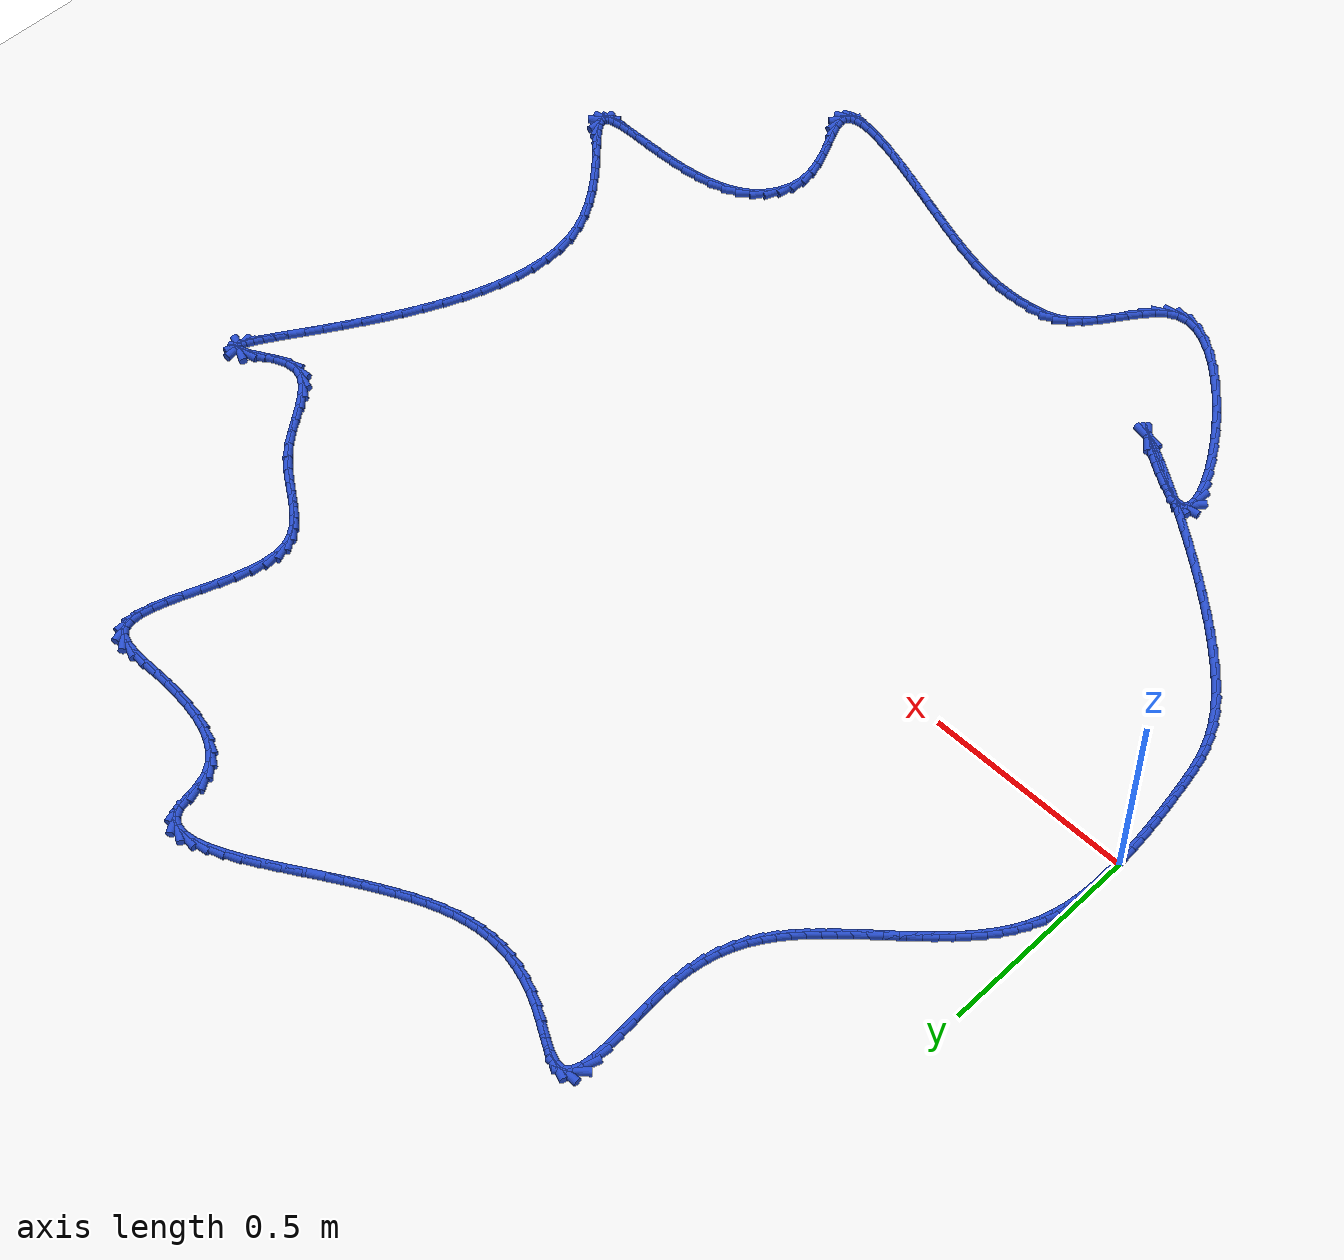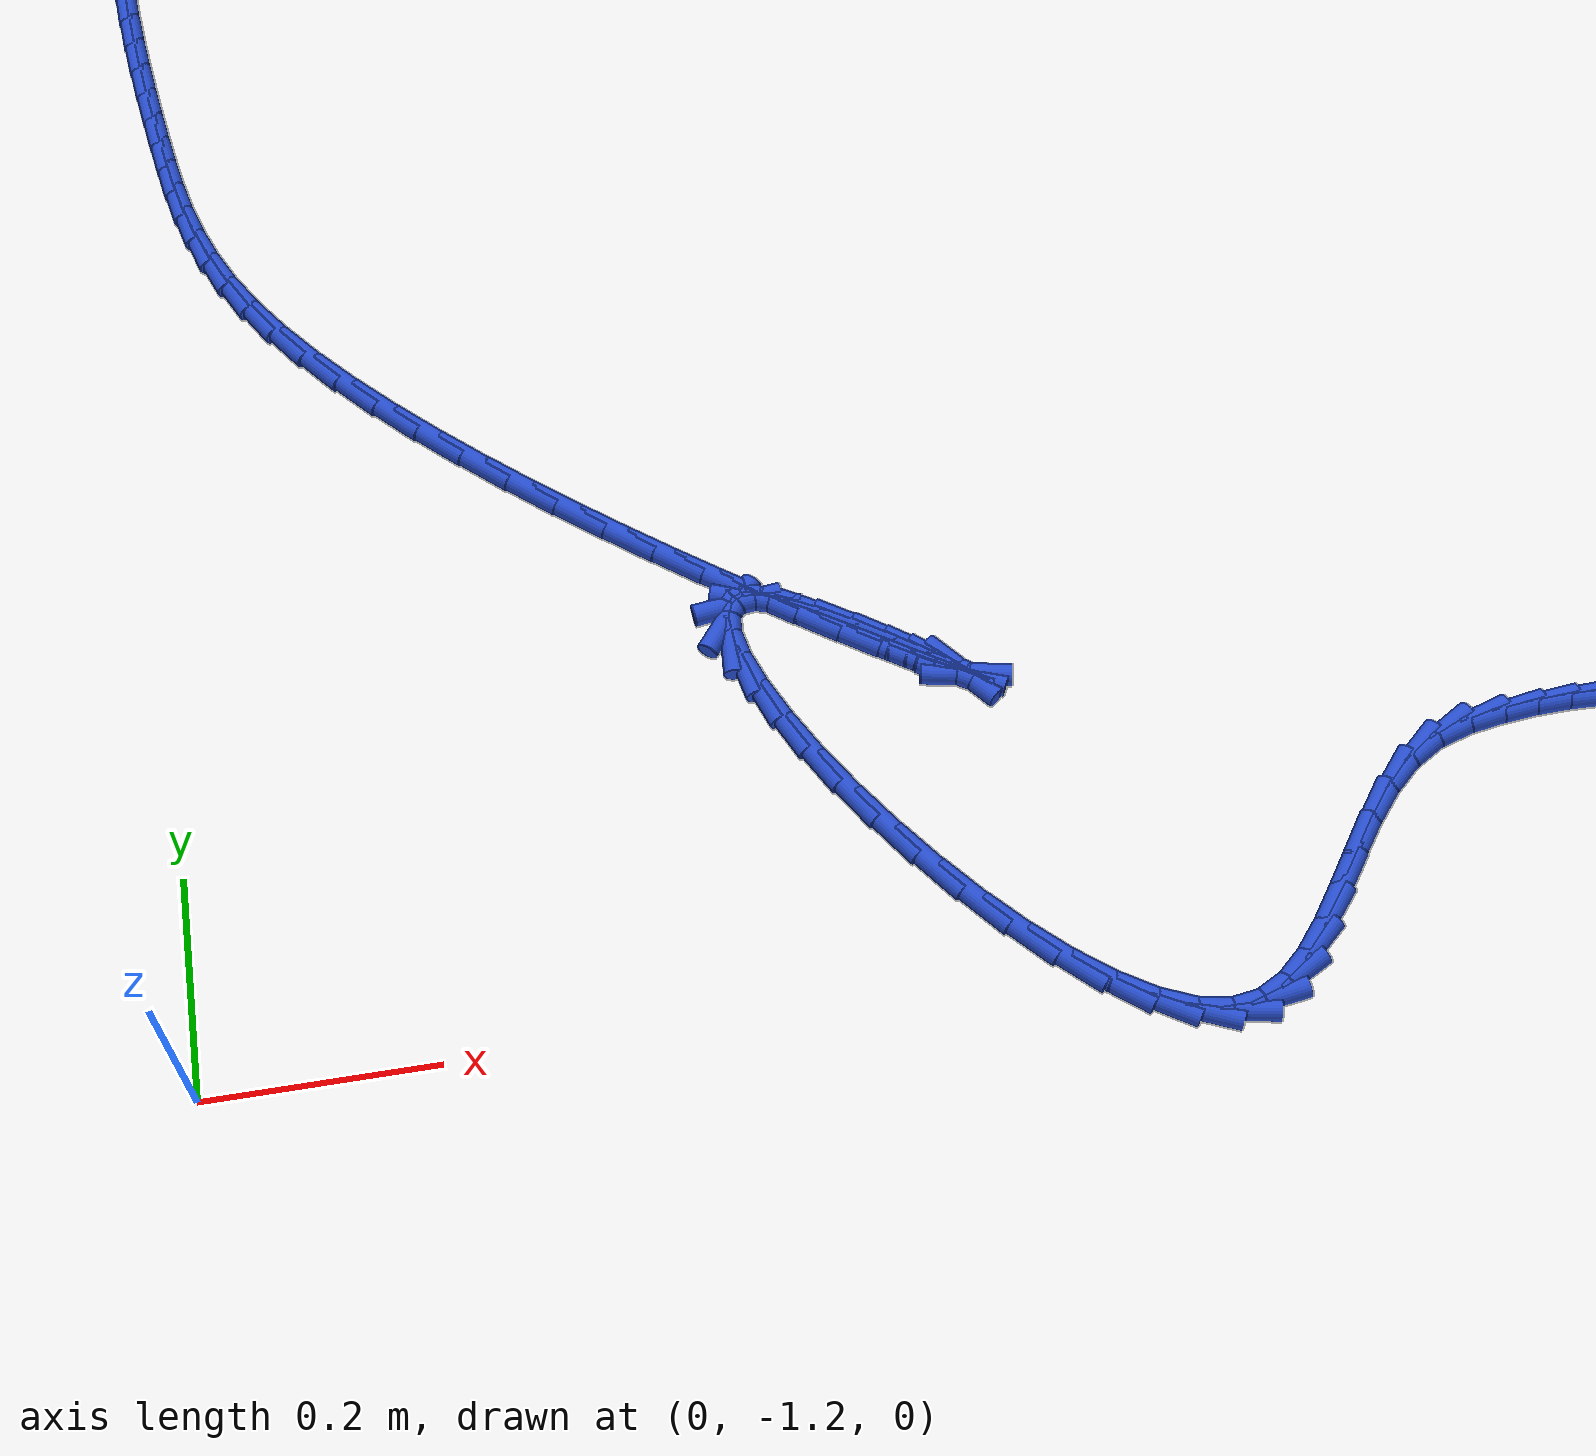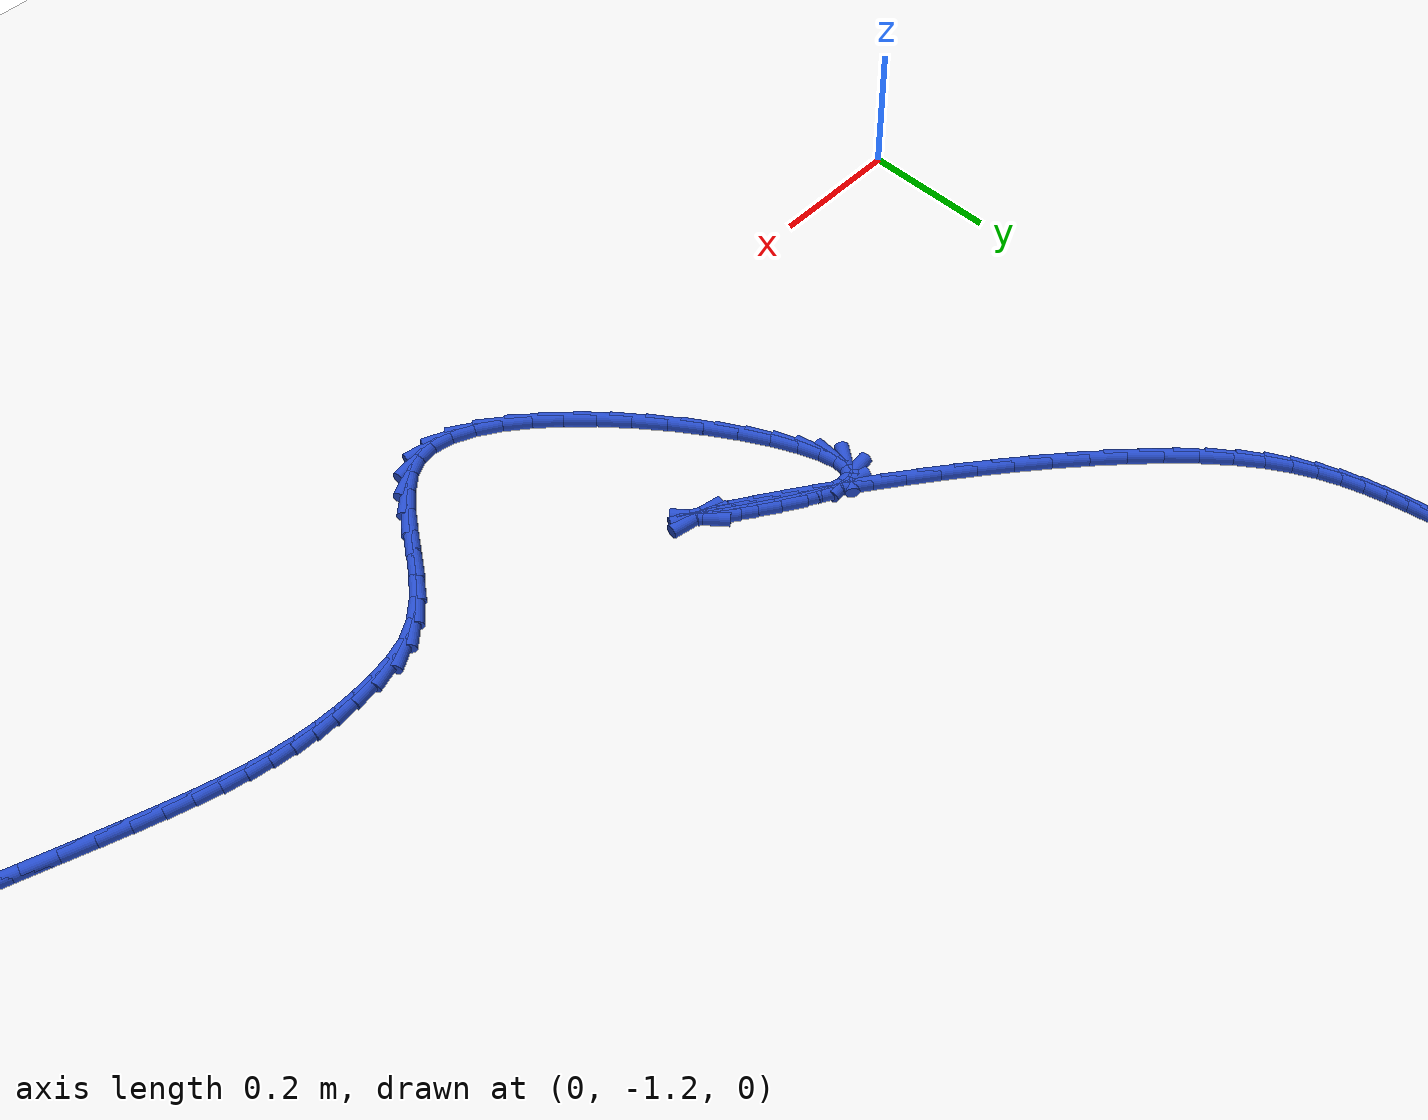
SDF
<sdf version="1.6">
 <world name="default">
  <light name="sun" type="directional">
   <pose>0 0 10 0 -0 0</pose>
   <diffuse>0.8 0.8 0.8 1</diffuse>
   <specular>0.2 0.2 0.2 1</specular>
   <attenuation>
    <range>1000</range>
    <constant>0.9</constant>
    <linear>0.01</linear>
    <quadratic>0.001</quadratic>
   </attenuation>
   <direction>-0.5 0.1 -0.9</direction>
  </light>
  <model name="ground_plane">
   <static>1</static>
   <link name="link">
    <collision name="collision">
     <geometry><plane><normal>0 0 1</normal><size>100 100</size></plane></geometry>
     <surface><friction><ode><mu>100</mu><mu2>50</mu2></ode></friction></surface>
    </collision>
    <visual name="visual">
     <cast_shadows>0</cast_shadows>
     <geometry><plane><normal>0 0 1</normal><size>100 100</size></plane></geometry>
     <material>
      <script><uri>file://media/materials/scripts/gazebo.material</uri><name>Gazebo/WhiteGlow</name></script>
     </material>
    </visual>
   </link>
  </model>
  <gravity>0 0 -9.8</gravity>
  <magnetic_field>6e-06 2.3e-05 -4.2e-05</magnetic_field>
  <atmosphere type="adiabatic"/>
  <physics name="default_physics" default="0" type="ode">
   <max_step_size>0.001</max_step_size>
   <real_time_factor>1</real_time_factor>
   <real_time_update_rate>1000</real_time_update_rate>
  </physics>
  <scene><ambient>0.4 0.4 0.4 1</ambient><background>0.7 0.7 0.7 1</background><shadows>1</shadows></scene>
  <spherical_coordinates>
   <surface_model>EARTH_WGS84</surface_model>
   <latitude_deg>0</latitude_deg>
   <longitude_deg>0</longitude_deg>
   <elevation>0</elevation>
   <heading_deg>0</heading_deg>
  </spherical_coordinates>
  <model name="line">
   <link name="link_0">
    <pose>-5.204170427930421e-18 -6.938893903907228e-18 0.01 0 1.57 -1.5384629921607185</pose>
    <collision name="collision">
     <geometry><cylinder><radius>0.01</radius><length>0.08</length></cylinder></geometry>
    </collision>
    <visual name="visual">
     <material>
      <script><name>Gazebo/Blue</name><uri>file://media/materials/scripts/gazebo.material</uri></script>
     </material>
     <geometry><cylinder><radius>0.01</radius><length>0.08</length></cylinder></geometry>
    </visual>
   </link>
   <link name="link_1">
    <pose>-0.0010594706275543749 0.03275571195729387 0.01 0 1.57 1.5702468868258193</pose>
    <collision name="collision">
     <geometry><cylinder><radius>0.01</radius><length>0.08</length></cylinder></geometry>
    </collision>
    <visual name="visual">
     <material>
      <script><name>Gazebo/Blue</name><uri>file://media/materials/scripts/gazebo.material</uri></script>
     </material>
     <geometry><cylinder><radius>0.01</radius><length>0.08</length></cylinder></geometry>
    </visual>
   </link>
   <link name="link_2">
    <pose>-0.001041490961238285 0.0654793314948731 0.01 0 1.57 1.5287290648702447</pose>
    <collision name="collision">
     <geometry><cylinder><radius>0.01</radius><length>0.08</length></cylinder></geometry>
    </collision>
    <visual name="visual">
     <material>
      <script><name>Gazebo/Blue</name><uri>file://media/materials/scripts/gazebo.material</uri></script>
     </material>
     <geometry><cylinder><radius>0.01</radius><length>0.08</length></cylinder></geometry>
    </visual>
   </link>
   <link name="link_3">
    <pose>0.00032615970830442197 0.09797119703147854 0.01 0 1.57 1.4778181368854744</pose>
    <collision name="collision">
     <geometry><cylinder><radius>0.01</radius><length>0.08</length></cylinder></geometry>
    </collision>
    <visual name="visual">
     <material>
      <script><name>Gazebo/Blue</name><uri>file://media/materials/scripts/gazebo.material</uri></script>
     </material>
     <geometry><cylinder><radius>0.01</radius><length>0.08</length></cylinder></geometry>
    </visual>
   </link>
   <link name="link_4">
    <pose>0.003315702090429911 0.13003164698585087 0.01 0 1.57 1.4166440280009087</pose>
    <collision name="collision">
     <geometry><cylinder><radius>0.01</radius><length>0.08</length></cylinder></geometry>
    </collision>
    <visual name="visual">
     <material>
      <script><name>Gazebo/Blue</name><uri>file://media/materials/scripts/gazebo.material</uri></script>
     </material>
     <geometry><cylinder><radius>0.01</radius><length>0.08</length></cylinder></geometry>
    </visual>
   </link>
   <link name="link_5">
    <pose>0.008199356894494341 0.16146101977673097 0.01 0 1.57 1.3443461245852795</pose>
    <collision name="collision">
     <geometry><cylinder><radius>0.01</radius><length>0.08</length></cylinder></geometry>
    </collision>
    <visual name="visual">
     <material>
      <script><name>Gazebo/Blue</name><uri>file://media/materials/scripts/gazebo.material</uri></script>
     </material>
     <geometry><cylinder><radius>0.01</radius><length>0.08</length></cylinder></geometry>
    </visual>
   </link>
   <link name="link_6">
    <pose>0.015249344829853876 0.19205965382285953 0.01 0 1.57 1.2602742645034584</pose>
    <collision name="collision">
     <geometry><cylinder><radius>0.01</radius><length>0.08</length></cylinder></geometry>
    </collision>
    <visual name="visual">
     <material>
      <script><name>Gazebo/Blue</name><uri>file://media/materials/scripts/gazebo.material</uri></script>
     </material>
     <geometry><cylinder><radius>0.01</radius><length>0.08</length></cylinder></geometry>
    </visual>
   </link>
   <link name="link_7">
    <pose>0.02473788660586467 0.2216278875429774 0.01 0 1.57 1.167350690738257</pose>
    <collision name="collision">
     <geometry><cylinder><radius>0.01</radius><length>0.08</length></cylinder></geometry>
    </collision>
    <visual name="visual">
     <material>
      <script><name>Gazebo/Blue</name><uri>file://media/materials/scripts/gazebo.material</uri></script>
     </material>
     <geometry><cylinder><radius>0.01</radius><length>0.08</length></cylinder></geometry>
    </visual>
   </link>
   <link name="link_8">
    <pose>0.03685466071494644 0.2500136667881283 0.01 0 1.57 1.0798755891489737</pose>
    <collision name="collision">
     <geometry><cylinder><radius>0.01</radius><length>0.08</length></cylinder></geometry>
    </collision>
    <visual name="visual">
     <material>
      <script><name>Gazebo/Blue</name><uri>file://media/materials/scripts/gazebo.material</uri></script>
     </material>
     <geometry><cylinder><radius>0.01</radius><length>0.08</length></cylinder></geometry>
    </visual>
   </link>
   <link name="link_9">
    <pose>0.051427165031165525 0.277273830384486 0.01 0 1.57 1.0026386375845382</pose>
    <collision name="collision">
     <geometry><cylinder><radius>0.01</radius><length>0.08</length></cylinder></geometry>
    </collision>
    <visual name="visual">
     <material>
      <script><name>Gazebo/Blue</name><uri>file://media/materials/scripts/gazebo.material</uri></script>
     </material>
     <geometry><cylinder><radius>0.01</radius><length>0.08</length></cylinder></geometry>
    </visual>
   </link>
   <link name="link_10">
    <pose>0.06818358833755174 0.3035224951306856 0.01 0 1.57 0.9360602095984024</pose>
    <collision name="collision">
     <geometry><cylinder><radius>0.01</radius><length>0.08</length></cylinder></geometry>
    </collision>
    <visual name="visual">
     <material>
      <script><name>Gazebo/Blue</name><uri>file://media/materials/scripts/gazebo.material</uri></script>
     </material>
     <geometry><cylinder><radius>0.01</radius><length>0.08</length></cylinder></geometry>
    </visual>
   </link>
   <link name="link_11">
    <pose>0.08685211676029808 0.32887377935773193 0.01 0 1.57 0.8800234178745512</pose>
    <collision name="collision">
     <geometry><cylinder><radius>0.01</radius><length>0.08</length></cylinder></geometry>
    </collision>
    <visual name="visual">
     <material>
      <script><name>Gazebo/Blue</name><uri>file://media/materials/scripts/gazebo.material</uri></script>
     </material>
     <geometry><cylinder><radius>0.01</radius><length>0.08</length></cylinder></geometry>
    </visual>
   </link>
   <link name="link_12">
    <pose>0.10716093642559762 0.3534418013966299 0.01 0 1.57 0.8341039650630805</pose>
    <collision name="collision">
     <geometry><cylinder><radius>0.01</radius><length>0.08</length></cylinder></geometry>
    </collision>
    <visual name="visual">
     <material>
      <script><name>Gazebo/Blue</name><uri>file://media/materials/scripts/gazebo.material</uri></script>
     </material>
     <geometry><cylinder><radius>0.01</radius><length>0.08</length></cylinder></geometry>
    </visual>
   </link>
   <link name="link_13">
    <pose>0.12883823345964324 0.37734067957838385 0.01 0 1.57 0.7977548447280498</pose>
    <collision name="collision">
     <geometry><cylinder><radius>0.01</radius><length>0.08</length></cylinder></geometry>
    </collision>
    <visual name="visual">
     <material>
      <script><name>Gazebo/Blue</name><uri>file://media/materials/scripts/gazebo.material</uri></script>
     </material>
     <geometry><cylinder><radius>0.01</radius><length>0.08</length></cylinder></geometry>
    </visual>
   </link>
   <link name="link_14">
    <pose>0.15161219398862796 0.4006845322339988 0.01 0 1.57 0.770435013168334</pose>
    <collision name="collision">
     <geometry><cylinder><radius>0.01</radius><length>0.08</length></cylinder></geometry>
    </collision>
    <visual name="visual">
     <material>
      <script><name>Gazebo/Blue</name><uri>file://media/materials/scripts/gazebo.material</uri></script>
     </material>
     <geometry><cylinder><radius>0.01</radius><length>0.08</length></cylinder></geometry>
    </visual>
   </link>
   <link name="link_15">
    <pose>0.1752110041387448 0.42358747769447935 0.01 0 1.57 0.7516904848797682</pose>
    <collision name="collision">
     <geometry><cylinder><radius>0.01</radius><length>0.08</length></cylinder></geometry>
    </collision>
    <visual name="visual">
     <material>
      <script><name>Gazebo/Blue</name><uri>file://media/materials/scripts/gazebo.material</uri></script>
     </material>
     <geometry><cylinder><radius>0.01</radius><length>0.08</length></cylinder></geometry>
    </visual>
   </link>
   <link name="link_16">
    <pose>0.19936285003618673 0.4461636342908303 0.01 0 1.57 0.7412018743576283</pose>
    <collision name="collision">
     <geometry><cylinder><radius>0.01</radius><length>0.08</length></cylinder></geometry>
    </collision>
    <visual name="visual">
     <material>
      <script><name>Gazebo/Blue</name><uri>file://media/materials/scripts/gazebo.material</uri></script>
     </material>
     <geometry><cylinder><radius>0.01</radius><length>0.08</length></cylinder></geometry>
    </visual>
   </link>
   <link name="link_17">
    <pose>0.2237959178071468 0.4685271203540563 0.01 0 1.57 0.7388109870767603</pose>
    <collision name="collision">
     <geometry><cylinder><radius>0.01</radius><length>0.08</length></cylinder></geometry>
    </collision>
    <visual name="visual">
     <material>
      <script><name>Gazebo/Blue</name><uri>file://media/materials/scripts/gazebo.material</uri></script>
     </material>
     <geometry><cylinder><radius>0.01</radius><length>0.08</length></cylinder></geometry>
    </visual>
   </link>
   <link name="link_18">
    <pose>0.2482383935778179 0.4907920542151622 0.01 0 1.57 0.7445352874370562</pose>
    <collision name="collision">
     <geometry><cylinder><radius>0.01</radius><length>0.08</length></cylinder></geometry>
    </collision>
    <visual name="visual">
     <material>
      <script><name>Gazebo/Blue</name><uri>file://media/materials/scripts/gazebo.material</uri></script>
     </material>
     <geometry><cylinder><radius>0.01</radius><length>0.08</length></cylinder></geometry>
    </visual>
   </link>
   <link name="link_19">
    <pose>0.27241846347439314 0.5130725542051526 0.01 0 1.57 0.7585749827108167</pose>
    <collision name="collision">
     <geometry><cylinder><radius>0.01</radius><length>0.08</length></cylinder></geometry>
    </collision>
    <visual name="visual">
     <material>
      <script><name>Gazebo/Blue</name><uri>file://media/materials/scripts/gazebo.material</uri></script>
     </material>
     <geometry><cylinder><radius>0.01</radius><length>0.08</length></cylinder></geometry>
    </visual>
   </link>
   <link name="link_20">
    <pose>0.29606431362306557 0.5354827386550325 0.01 0 1.57 0.781313469718438</pose>
    <collision name="collision">
     <geometry><cylinder><radius>0.01</radius><length>0.08</length></cylinder></geometry>
    </collision>
    <visual name="visual">
     <material>
      <script><name>Gazebo/Blue</name><uri>file://media/materials/scripts/gazebo.material</uri></script>
     </material>
     <geometry><cylinder><radius>0.01</radius><length>0.08</length></cylinder></geometry>
    </visual>
   </link>
   <link name="link_21">
    <pose>0.3189041301500279 0.5581367258958061 0.01 0 1.57 0.8133076241221955</pose>
    <collision name="collision">
     <geometry><cylinder><radius>0.01</radius><length>0.08</length></cylinder></geometry>
    </collision>
    <visual name="visual">
     <material>
      <script><name>Gazebo/Blue</name><uri>file://media/materials/scripts/gazebo.material</uri></script>
     </material>
     <geometry><cylinder><radius>0.01</radius><length>0.08</length></cylinder></geometry>
    </visual>
   </link>
   <link name="link_22">
    <pose>0.34066609918147345 0.5811486342584786 0.01 0 1.57 0.8552592795555024</pose>
    <collision name="collision">
     <geometry><cylinder><radius>0.01</radius><length>0.08</length></cylinder></geometry>
    </collision>
    <visual name="visual">
     <material>
      <script><name>Gazebo/Blue</name><uri>file://media/materials/scripts/gazebo.material</uri></script>
     </material>
     <geometry><cylinder><radius>0.01</radius><length>0.08</length></cylinder></geometry>
    </visual>
   </link>
   <link name="link_23">
    <pose>0.36107840684359505 0.6046325820740548 0.01 0 1.57 0.9080407438181826</pose>
    <collision name="collision">
     <geometry><cylinder><radius>0.01</radius><length>0.08</length></cylinder></geometry>
    </collision>
    <visual name="visual">
     <material>
      <script><name>Gazebo/Blue</name><uri>file://media/materials/scripts/gazebo.material</uri></script>
     </material>
     <geometry><cylinder><radius>0.01</radius><length>0.08</length></cylinder></geometry>
    </visual>
   </link>
   <link name="link_24">
    <pose>0.3798797425106135 0.6287204984050254 0.01 0 1.57 0.9726077621093715</pose>
    <collision name="collision">
     <geometry><cylinder><radius>0.01</radius><length>0.08</length></cylinder></geometry>
    </collision>
    <visual name="visual">
     <material>
      <script><name>Gazebo/Blue</name><uri>file://media/materials/scripts/gazebo.material</uri></script>
     </material>
     <geometry><cylinder><radius>0.01</radius><length>0.08</length></cylinder></geometry>
    </visual>
   </link>
   <link name="link_25">
    <pose>0.39688655146858387 0.653676165780874 0.01 0 1.57 1.0481157510346502</pose>
    <collision name="collision">
     <geometry><cylinder><radius>0.01</radius><length>0.08</length></cylinder></geometry>
    </collision>
    <visual name="visual">
     <material>
      <script><name>Gazebo/Blue</name><uri>file://media/materials/scripts/gazebo.material</uri></script>
     </material>
     <geometry><cylinder><radius>0.01</radius><length>0.08</length></cylinder></geometry>
    </visual>
   </link>
   <link name="link_26">
    <pose>0.4119501805029849 0.6798225504457849 0.01 0 1.57 1.132276816492037</pose>
    <collision name="collision">
     <geometry><cylinder><radius>0.01</radius><length>0.08</length></cylinder></geometry>
    </collision>
    <visual name="visual">
     <material>
      <script><name>Gazebo/Blue</name><uri>file://media/materials/scripts/gazebo.material</uri></script>
     </material>
     <geometry><cylinder><radius>0.01</radius><length>0.08</length></cylinder></geometry>
    </visual>
   </link>
   <link name="link_27">
    <pose>0.42492214212641344 0.7074828996733143 0.01 0 1.57 1.2218630214811355</pose>
    <collision name="collision">
     <geometry><cylinder><radius>0.01</radius><length>0.08</length></cylinder></geometry>
    </collision>
    <visual name="visual">
     <material>
      <script><name>Gazebo/Blue</name><uri>file://media/materials/scripts/gazebo.material</uri></script>
     </material>
     <geometry><cylinder><radius>0.01</radius><length>0.08</length></cylinder></geometry>
    </visual>
   </link>
   <link name="link_28">
    <pose>0.4356539488514664 0.7369804607370186 0.01 0 1.57 1.3131150013466104</pose>
    <collision name="collision">
     <geometry><cylinder><radius>0.01</radius><length>0.08</length></cylinder></geometry>
    </collision>
    <visual name="visual">
     <material>
      <script><name>Gazebo/Blue</name><uri>file://media/materials/scripts/gazebo.material</uri></script>
     </material>
     <geometry><cylinder><radius>0.01</radius><length>0.08</length></cylinder></geometry>
    </visual>
   </link>
   <link name="link_29">
    <pose>0.4439971131907408 0.7686384809104544 0.01 0 1.57 1.402350917145807</pose>
    <collision name="collision">
     <geometry><cylinder><radius>0.01</radius><length>0.08</length></cylinder></geometry>
    </collision>
    <visual name="visual">
     <material>
      <script><name>Gazebo/Blue</name><uri>file://media/materials/scripts/gazebo.material</uri></script>
     </material>
     <geometry><cylinder><radius>0.01</radius><length>0.08</length></cylinder></geometry>
    </visual>
   </link>
   <link name="link_30">
    <pose>0.4498031476568334 0.8027802074671776 0.01 0 1.57 1.4865435165023273</pose>
    <collision name="collision">
     <geometry><cylinder><radius>0.01</radius><length>0.08</length></cylinder></geometry>
    </collision>
    <visual name="visual">
     <material>
      <script><name>Gazebo/Blue</name><uri>file://media/materials/scripts/gazebo.material</uri></script>
     </material>
     <geometry><cylinder><radius>0.01</radius><length>0.08</length></cylinder></geometry>
    </visual>
   </link>
   <link name="link_31">
    <pose>0.452923564762341 0.8397288876807449 0.01 0 1.57 1.562304591862251</pose>
    <collision name="collision">
     <geometry><cylinder><radius>0.01</radius><length>0.08</length></cylinder></geometry>
    </collision>
    <visual name="visual">
     <material>
      <script><name>Gazebo/Blue</name><uri>file://media/materials/scripts/gazebo.material</uri></script>
     </material>
     <geometry><cylinder><radius>0.01</radius><length>0.08</length></cylinder></geometry>
    </visual>
   </link>
   <link name="link_32">
    <pose>0.45326319179582636 0.8797229375053843 0.01 0 1.57 -1.5270688987369447</pose>
    <collision name="collision">
     <geometry><cylinder><radius>0.01</radius><length>0.08</length></cylinder></geometry>
    </collision>
    <visual name="visual">
     <material>
      <script><name>Gazebo/Blue</name><uri>file://media/materials/scripts/gazebo.material</uri></script>
     </material>
     <geometry><cylinder><radius>0.01</radius><length>0.08</length></cylinder></geometry>
    </visual>
   </link>
   <link name="link_33">
    <pose>0.451417649953982 0.921901622471293 0.01 0 1.57 -1.5018023446379443</pose>
    <collision name="collision">
     <geometry><cylinder><radius>0.01</radius><length>0.08</length></cylinder></geometry>
    </collision>
    <visual name="visual">
     <material>
      <script><name>Gazebo/Blue</name><uri>file://media/materials/scripts/gazebo.material</uri></script>
     </material>
     <geometry><cylinder><radius>0.01</radius><length>0.08</length></cylinder></geometry>
    </visual>
   </link>
   <link name="link_34">
    <pose>0.4484644470323517 0.9646374586436969 0.01 0 1.57 -1.4995237731716504</pose>
    <collision name="collision">
     <geometry><cylinder><radius>0.01</radius><length>0.08</length></cylinder></geometry>
    </collision>
    <visual name="visual">
     <material>
      <script><name>Gazebo/Blue</name><uri>file://media/materials/scripts/gazebo.material</uri></script>
     </material>
     <geometry><cylinder><radius>0.01</radius><length>0.08</length></cylinder></geometry>
    </visual>
   </link>
   <link name="link_35">
    <pose>0.445490917989463 1.006287325687106 0.01 0 1.57 -1.5218508118113179</pose>
    <collision name="collision">
     <geometry><cylinder><radius>0.01</radius><length>0.08</length></cylinder></geometry>
    </collision>
    <visual name="visual">
     <material>
      <script><name>Gazebo/Blue</name><uri>file://media/materials/scripts/gazebo.material</uri></script>
     </material>
     <geometry><cylinder><radius>0.01</radius><length>0.08</length></cylinder></geometry>
    </visual>
   </link>
   <link name="link_36">
    <pose>0.44358439778384273 1.0452081032660305 0.01 0 1.57 1.563623255502099</pose>
    <collision name="collision">
     <geometry><cylinder><radius>0.01</radius><length>0.08</length></cylinder></geometry>
    </collision>
    <visual name="visual">
     <material>
      <script><name>Gazebo/Blue</name><uri>file://media/materials/scripts/gazebo.material</uri></script>
     </material>
     <geometry><cylinder><radius>0.01</radius><length>0.08</length></cylinder></geometry>
    </visual>
   </link>
   <link name="link_37">
    <pose>0.4438322213740182 1.0797566710449802 0.01 0 1.57 1.4491045600259156</pose>
    <collision name="collision">
     <geometry><cylinder><radius>0.01</radius><length>0.08</length></cylinder></geometry>
    </collision>
    <visual name="visual">
     <material>
      <script><name>Gazebo/Blue</name><uri>file://media/materials/scripts/gazebo.material</uri></script>
     </material>
     <geometry><cylinder><radius>0.01</radius><length>0.08</length></cylinder></geometry>
    </visual>
   </link>
   <link name="link_38">
    <pose>0.4473217237185165 1.1082899086884652 0.01 0 1.57 1.2124259270177387</pose>
    <collision name="collision">
     <geometry><cylinder><radius>0.01</radius><length>0.08</length></cylinder></geometry>
    </collision>
    <visual name="visual">
     <material>
      <script><name>Gazebo/Blue</name><uri>file://media/materials/scripts/gazebo.material</uri></script>
     </material>
     <geometry><cylinder><radius>0.01</radius><length>0.08</length></cylinder></geometry>
    </visual>
   </link>
   <link name="link_39">
    <pose>0.4551402397758649 1.1291646958609953 0.01 0 1.57 0.7185179351799432</pose>
    <collision name="collision">
     <geometry><cylinder><radius>0.01</radius><length>0.08</length></cylinder></geometry>
    </collision>
    <visual name="visual">
     <material>
      <script><name>Gazebo/Blue</name><uri>file://media/materials/scripts/gazebo.material</uri></script>
     </material>
     <geometry><cylinder><radius>0.01</radius><length>0.08</length></cylinder></geometry>
    </visual>
   </link>
   <link name="link_40">
    <pose>0.46837510450459013 1.1407379122270802 0.01 0 1.57 0.03899752587914408</pose>
    <collision name="collision">
     <geometry><cylinder><radius>0.01</radius><length>0.08</length></cylinder></geometry>
    </collision>
    <visual name="visual">
     <material>
      <script><name>Gazebo/Blue</name><uri>file://media/materials/scripts/gazebo.material</uri></script>
     </material>
     <geometry><cylinder><radius>0.01</radius><length>0.08</length></cylinder></geometry>
    </visual>
   </link>
   <link name="link_41">
    <pose>0.48803439375470553 1.1415049647540974 0.01 0 1.57 -0.3367340852690993</pose>
    <collision name="collision">
     <geometry><cylinder><radius>0.01</radius><length>0.08</length></cylinder></geometry>
    </collision>
    <visual name="visual">
     <material>
      <script><name>Gazebo/Blue</name><uri>file://media/materials/scripts/gazebo.material</uri></script>
     </material>
     <geometry><cylinder><radius>0.01</radius><length>0.08</length></cylinder></geometry>
    </visual>
   </link>
   <link name="link_42">
    <pose>0.513652505792524 1.13253692123619 0.01 0 1.57 -0.4756875289552192</pose>
    <collision name="collision">
     <geometry><cylinder><radius>0.01</radius><length>0.08</length></cylinder></geometry>
    </collision>
    <visual name="visual">
     <material>
      <script><name>Gazebo/Blue</name><uri>file://media/materials/scripts/gazebo.material</uri></script>
     </material>
     <geometry><cylinder><radius>0.01</radius><length>0.08</length></cylinder></geometry>
    </visual>
   </link>
   <link name="link_43">
    <pose>0.5434614882937465 1.1171810687952972 0.01 0 1.57 -0.5173974170125976</pose>
    <collision name="collision">
     <geometry><cylinder><radius>0.01</radius><length>0.08</length></cylinder></geometry>
    </collision>
    <visual name="visual">
     <material>
      <script><name>Gazebo/Blue</name><uri>file://media/materials/scripts/gazebo.material</uri></script>
     </material>
     <geometry><cylinder><radius>0.01</radius><length>0.08</length></cylinder></geometry>
    </visual>
   </link>
   <link name="link_44">
    <pose>0.5756485593789893 1.0988630466503102 0.01 0 1.57 -0.49914095550639814</pose>
    <collision name="collision">
     <geometry><cylinder><radius>0.01</radius><length>0.08</length></cylinder></geometry>
    </collision>
    <visual name="visual">
     <material>
      <script><name>Gazebo/Blue</name><uri>file://media/materials/scripts/gazebo.material</uri></script>
     </material>
     <geometry><cylinder><radius>0.01</radius><length>0.08</length></cylinder></geometry>
    </visual>
   </link>
   <link name="link_45">
    <pose>0.6084022188891854 1.0810061579729695 0.01 0 1.57 -0.4352174981019442</pose>
    <collision name="collision">
     <geometry><cylinder><radius>0.01</radius><length>0.08</length></cylinder></geometry>
    </collision>
    <visual name="visual">
     <material>
      <script><name>Gazebo/Blue</name><uri>file://media/materials/scripts/gazebo.material</uri></script>
     </material>
     <geometry><cylinder><radius>0.01</radius><length>0.08</length></cylinder></geometry>
    </visual>
   </link>
   <link name="link_46">
    <pose>0.6404100518903886 1.0661240795502986 0.01 0 1.57 -0.3581395807517648</pose>
    <collision name="collision">
     <geometry><cylinder><radius>0.01</radius><length>0.08</length></cylinder></geometry>
    </collision>
    <visual name="visual">
     <material>
      <script><name>Gazebo/Blue</name><uri>file://media/materials/scripts/gazebo.material</uri></script>
     </material>
     <geometry><cylinder><radius>0.01</radius><length>0.08</length></cylinder></geometry>
    </visual>
   </link>
   <link name="link_47">
    <pose>0.6716134879758556 1.0544452470784809 0.01 0 1.57 -0.27454881219492805</pose>
    <collision name="collision">
     <geometry><cylinder><radius>0.01</radius><length>0.08</length></cylinder></geometry>
    </collision>
    <visual name="visual">
     <material>
      <script><name>Gazebo/Blue</name><uri>file://media/materials/scripts/gazebo.material</uri></script>
     </material>
     <geometry><cylinder><radius>0.01</radius><length>0.08</length></cylinder></geometry>
    </visual>
   </link>
   <link name="link_48">
    <pose>0.7021477320030255 1.0458449239213334 0.01 0 1.57 -0.18604025595041354</pose>
    <collision name="collision">
     <geometry><cylinder><radius>0.01</radius><length>0.08</length></cylinder></geometry>
    </collision>
    <visual name="visual">
     <material>
      <script><name>Gazebo/Blue</name><uri>file://media/materials/scripts/gazebo.material</uri></script>
     </material>
     <geometry><cylinder><radius>0.01</radius><length>0.08</length></cylinder></geometry>
    </visual>
   </link>
   <link name="link_49">
    <pose>0.7321479888293365 1.0401983734426734 0.01 0 1.57 -0.09489567620135819</pose>
    <collision name="collision">
     <geometry><cylinder><radius>0.01</radius><length>0.08</length></cylinder></geometry>
    </collision>
    <visual name="visual">
     <material>
      <script><name>Gazebo/Blue</name><uri>file://media/materials/scripts/gazebo.material</uri></script>
     </material>
     <geometry><cylinder><radius>0.01</radius><length>0.08</length></cylinder></geometry>
    </visual>
   </link>
   <link name="link_50">
    <pose>0.7617494633122276 1.037380859006318 0.01 0 1.57 -0.003858983766080388</pose>
    <collision name="collision">
     <geometry><cylinder><radius>0.01</radius><length>0.08</length></cylinder></geometry>
    </collision>
    <visual name="visual">
     <material>
      <script><name>Gazebo/Blue</name><uri>file://media/materials/scripts/gazebo.material</uri></script>
     </material>
     <geometry><cylinder><radius>0.01</radius><length>0.08</length></cylinder></geometry>
    </visual>
   </link>
   <link name="link_51">
    <pose>0.791087360309137 1.0372676439760853 0.01 0 1.57 0.08423661307787737</pose>
    <collision name="collision">
     <geometry><cylinder><radius>0.01</radius><length>0.08</length></cylinder></geometry>
    </collision>
    <visual name="visual">
     <material>
      <script><name>Gazebo/Blue</name><uri>file://media/materials/scripts/gazebo.material</uri></script>
     </material>
     <geometry><cylinder><radius>0.01</radius><length>0.08</length></cylinder></geometry>
    </visual>
   </link>
   <link name="link_52">
    <pose>0.8202968846775037 1.0397339917157915 0.01 0 1.57 0.1668726121571206</pose>
    <collision name="collision">
     <geometry><cylinder><radius>0.01</radius><length>0.08</length></cylinder></geometry>
    </collision>
    <visual name="visual">
     <material>
      <script><name>Gazebo/Blue</name><uri>file://media/materials/scripts/gazebo.material</uri></script>
     </material>
     <geometry><cylinder><radius>0.01</radius><length>0.08</length></cylinder></geometry>
    </visual>
   </link>
   <link name="link_53">
    <pose>0.8495132412747664 1.044655165589255 0.01 0 1.57 0.24214480410317143</pose>
    <collision name="collision">
     <geometry><cylinder><radius>0.01</radius><length>0.08</length></cylinder></geometry>
    </collision>
    <visual name="visual">
     <material>
      <script><name>Gazebo/Blue</name><uri>file://media/materials/scripts/gazebo.material</uri></script>
     </material>
     <geometry><cylinder><radius>0.01</radius><length>0.08</length></cylinder></geometry>
    </visual>
   </link>
   <link name="link_54">
    <pose>0.8788716349583637 1.0519064289602928 0.01 0 1.57 0.30888280600090806</pose>
    <collision name="collision">
     <geometry><cylinder><radius>0.01</radius><length>0.08</length></cylinder></geometry>
    </collision>
    <visual name="visual">
     <material>
      <script><name>Gazebo/Blue</name><uri>file://media/materials/scripts/gazebo.material</uri></script>
     </material>
     <geometry><cylinder><radius>0.01</radius><length>0.08</length></cylinder></geometry>
    </visual>
   </link>
   <link name="link_55">
    <pose>0.9085072705857342 1.0613630451927218 0.01 0 1.57 0.3666019316522715</pose>
    <collision name="collision">
     <geometry><cylinder><radius>0.01</radius><length>0.08</length></cylinder></geometry>
    </collision>
    <visual name="visual">
     <material>
      <script><name>Gazebo/Blue</name><uri>file://media/materials/scripts/gazebo.material</uri></script>
     </material>
     <geometry><cylinder><radius>0.01</radius><length>0.08</length></cylinder></geometry>
    </visual>
   </link>
   <link name="link_56">
    <pose>0.9385553530143166 1.07290027765036 0.01 0 1.57 0.4153551293805062</pose>
    <collision name="collision">
     <geometry><cylinder><radius>0.01</radius><length>0.08</length></cylinder></geometry>
    </collision>
    <visual name="visual">
     <material>
      <script><name>Gazebo/Blue</name><uri>file://media/materials/scripts/gazebo.material</uri></script>
     </material>
     <geometry><cylinder><radius>0.01</radius><length>0.08</length></cylinder></geometry>
    </visual>
   </link>
   <link name="link_57">
    <pose>0.9691510871015495 1.0863933896970244 0.01 0 1.57 0.4555575314570801</pose>
    <collision name="collision">
     <geometry><cylinder><radius>0.01</radius><length>0.08</length></cylinder></geometry>
    </collision>
    <visual name="visual">
     <material>
      <script><name>Gazebo/Blue</name><uri>file://media/materials/scripts/gazebo.material</uri></script>
     </material>
     <geometry><cylinder><radius>0.01</radius><length>0.08</length></cylinder></geometry>
    </visual>
   </link>
   <link name="link_58">
    <pose>1.0004296777048713 1.1017176446965316 0.01 0 1.57 0.4878312058477289</pose>
    <collision name="collision">
     <geometry><cylinder><radius>0.01</radius><length>0.08</length></cylinder></geometry>
    </collision>
    <visual name="visual">
     <material>
      <script><name>Gazebo/Blue</name><uri>file://media/materials/scripts/gazebo.material</uri></script>
     </material>
     <geometry><cylinder><radius>0.01</radius><length>0.08</length></cylinder></geometry>
    </visual>
   </link>
   <link name="link_59">
    <pose>1.0325263296817215 1.1187483060127004 0.01 0 1.57 0.5128892839694739</pose>
    <collision name="collision">
     <geometry><cylinder><radius>0.01</radius><length>0.08</length></cylinder></geometry>
    </collision>
    <visual name="visual">
     <material>
      <script><name>Gazebo/Blue</name><uri>file://media/materials/scripts/gazebo.material</uri></script>
     </material>
     <geometry><cylinder><radius>0.01</radius><length>0.08</length></cylinder></geometry>
    </visual>
   </link>
   <link name="link_60">
    <pose>1.0655762478895379 1.1373606370093472 0.01 0 1.57 0.5314598005480564</pose>
    <collision name="collision">
     <geometry><cylinder><radius>0.01</radius><length>0.08</length></cylinder></geometry>
    </collision>
    <visual name="visual">
     <material>
      <script><name>Gazebo/Blue</name><uri>file://media/materials/scripts/gazebo.material</uri></script>
     </material>
     <geometry><cylinder><radius>0.01</radius><length>0.08</length></cylinder></geometry>
    </visual>
   </link>
   <link name="link_61">
    <pose>1.0997146371857591 1.157429901050289 0.01 0 1.57 0.5442412671821478</pose>
    <collision name="collision">
     <geometry><cylinder><radius>0.01</radius><length>0.08</length></cylinder></geometry>
    </collision>
    <visual name="visual">
     <material>
      <script><name>Gazebo/Blue</name><uri>file://media/materials/scripts/gazebo.material</uri></script>
     </material>
     <geometry><cylinder><radius>0.01</radius><length>0.08</length></cylinder></geometry>
    </visual>
   </link>
   <link name="link_62">
    <pose>1.135076702427824 1.1788313614993438 0.01 0 1.57 0.5518592015569649</pose>
    <collision name="collision">
     <geometry><cylinder><radius>0.01</radius><length>0.08</length></cylinder></geometry>
    </collision>
    <visual name="visual">
     <material>
      <script><name>Gazebo/Blue</name><uri>file://media/materials/scripts/gazebo.material</uri></script>
     </material>
     <geometry><cylinder><radius>0.01</radius><length>0.08</length></cylinder></geometry>
    </visual>
   </link>
   <link name="link_63">
    <pose>1.1717953141727884 1.2014377699256131 0.01 0 1.57 0.5523546900034856</pose>
    <collision name="collision">
     <geometry><cylinder><radius>0.01</radius><length>0.08</length></cylinder></geometry>
    </collision>
    <visual name="visual">
     <material>
      <script><name>Gazebo/Blue</name><uri>file://media/materials/scripts/gazebo.material</uri></script>
     </material>
     <geometry><cylinder><radius>0.01</radius><length>0.08</length></cylinder></geometry>
    </visual>
   </link>
   <link name="link_64">
    <pose>1.209710534994802 1.224806805532491 0.01 0 1.57 0.5412774371412772</pose>
    <collision name="collision">
     <geometry><cylinder><radius>0.01</radius><length>0.08</length></cylinder></geometry>
    </collision>
    <visual name="visual">
     <material>
      <script><name>Gazebo/Blue</name><uri>file://media/materials/scripts/gazebo.material</uri></script>
     </material>
     <geometry><cylinder><radius>0.01</radius><length>0.08</length></cylinder></geometry>
    </visual>
   </link>
   <link name="link_65">
    <pose>1.2480880930259786 1.2478781421344274 0.01 0 1.57 0.5172607967081113</pose>
    <collision name="collision">
     <geometry><cylinder><radius>0.01</radius><length>0.08</length></cylinder></geometry>
    </collision>
    <visual name="visual">
     <material>
      <script><name>Gazebo/Blue</name><uri>file://media/materials/scripts/gazebo.material</uri></script>
     </material>
     <geometry><cylinder><radius>0.01</radius><length>0.08</length></cylinder></geometry>
    </visual>
   </link>
   <link name="link_66">
    <pose>1.2861269325055669 1.269519591573711 0.01 0 1.57 0.477209621101128</pose>
    <collision name="collision">
     <geometry><cylinder><radius>0.01</radius><length>0.08</length></cylinder></geometry>
    </collision>
    <visual name="visual">
     <material>
      <script><name>Gazebo/Blue</name><uri>file://media/materials/scripts/gazebo.material</uri></script>
     </material>
     <geometry><cylinder><radius>0.01</radius><length>0.08</length></cylinder></geometry>
    </visual>
   </link>
   <link name="link_67">
    <pose>1.3230259976728154 1.288598965692632 0.01 0 1.57 0.41459044498921754</pose>
    <collision name="collision">
     <geometry><cylinder><radius>0.01</radius><length>0.08</length></cylinder></geometry>
    </collision>
    <visual name="visual">
     <material>
      <script><name>Gazebo/Blue</name><uri>file://media/materials/scripts/gazebo.material</uri></script>
     </material>
     <geometry><cylinder><radius>0.01</radius><length>0.08</length></cylinder></geometry>
    </visual>
   </link>
   <link name="link_68">
    <pose>1.357984232766973 1.3039840763334787 0.01 0 1.57 0.31671017357711156</pose>
    <collision name="collision">
     <geometry><cylinder><radius>0.01</radius><length>0.08</length></cylinder></geometry>
    </collision>
    <visual name="visual">
     <material>
      <script><name>Gazebo/Blue</name><uri>file://media/materials/scripts/gazebo.material</uri></script>
     </material>
     <geometry><cylinder><radius>0.01</radius><length>0.08</length></cylinder></geometry>
    </visual>
   </link>
   <link name="link_69">
    <pose>1.3902005820272887 1.3145427353385408 0.01 0 1.57 0.15907261105636522</pose>
    <collision name="collision">
     <geometry><cylinder><radius>0.01</radius><length>0.08</length></cylinder></geometry>
    </collision>
    <visual name="visual">
     <material>
      <script><name>Gazebo/Blue</name><uri>file://media/materials/scripts/gazebo.material</uri></script>
     </material>
     <geometry><cylinder><radius>0.01</radius><length>0.08</length></cylinder></geometry>
    </visual>
   </link>
   <link name="link_70">
    <pose>1.4188739896930114 1.3191427545501075 0.01 0 1.57 -0.10202305257384771</pose>
    <collision name="collision">
     <geometry><cylinder><radius>0.01</radius><length>0.08</length></cylinder></geometry>
    </collision>
    <visual name="visual">
     <material>
      <script><name>Gazebo/Blue</name><uri>file://media/materials/scripts/gazebo.material</uri></script>
     </material>
     <geometry><cylinder><radius>0.01</radius><length>0.08</length></cylinder></geometry>
    </visual>
   </link>
   <link name="link_71">
    <pose>1.44320340000339 1.3166519458104688 0.01 0 1.57 -0.5093203163931969</pose>
    <collision name="collision">
     <geometry><cylinder><radius>0.01</radius><length>0.08</length></cylinder></geometry>
    </collision>
    <visual name="visual">
     <material>
      <script><name>Gazebo/Blue</name><uri>file://media/materials/scripts/gazebo.material</uri></script>
     </material>
     <geometry><cylinder><radius>0.01</radius><length>0.08</length></cylinder></geometry>
    </visual>
   </link>
   <link name="link_72">
    <pose>1.4623877571976727 1.3059381209619132 0.01 0 1.57 -0.9876764601237008</pose>
    <collision name="collision">
     <geometry><cylinder><radius>0.01</radius><length>0.08</length></cylinder></geometry>
    </collision>
    <visual name="visual">
     <material>
      <script><name>Gazebo/Blue</name><uri>file://media/materials/scripts/gazebo.material</uri></script>
     </material>
     <geometry><cylinder><radius>0.01</radius><length>0.08</length></cylinder></geometry>
    </visual>
   </link>
   <link name="link_73">
    <pose>1.4756260159098262 1.2858691046891282 0.01 0 1.57 -1.315060683871717</pose>
    <collision name="collision">
     <geometry><cylinder><radius>0.01</radius><length>0.08</length></cylinder></geometry>
    </collision>
    <visual name="visual">
     <material>
      <script><name>Gazebo/Blue</name><uri>file://media/materials/scripts/gazebo.material</uri></script>
     </material>
     <geometry><cylinder><radius>0.01</radius><length>0.08</length></cylinder></geometry>
    </visual>
   </link>
   <link name="link_74">
    <pose>1.483249513755391 1.2567117509358015 0.01 0 1.57 -1.3721608666009506</pose>
    <collision name="collision">
     <geometry><cylinder><radius>0.01</radius><length>0.08</length></cylinder></geometry>
    </collision>
    <visual name="visual">
     <material>
      <script><name>Gazebo/Blue</name><uri>file://media/materials/scripts/gazebo.material</uri></script>
     </material>
     <geometry><cylinder><radius>0.01</radius><length>0.08</length></cylinder></geometry>
    </visual>
   </link>
   <link name="link_75">
    <pose>1.4898377892947974 1.2239814536861517 0.01 0 1.57 -1.2237694278271536</pose>
    <collision name="collision">
     <geometry><cylinder><radius>0.01</radius><length>0.08</length></cylinder></geometry>
    </collision>
    <visual name="visual">
     <material>
      <script><name>Gazebo/Blue</name><uri>file://media/materials/scripts/gazebo.material</uri></script>
     </material>
     <geometry><cylinder><radius>0.01</radius><length>0.08</length></cylinder></geometry>
    </visual>
   </link>
   <link name="link_76">
    <pose>1.5006561989146605 1.1940684874368372 0.01 0 1.57 -0.9787365424061897</pose>
    <collision name="collision">
     <geometry><cylinder><radius>0.01</radius><length>0.08</length></cylinder></geometry>
    </collision>
    <visual name="visual">
     <material>
      <script><name>Gazebo/Blue</name><uri>file://media/materials/scripts/gazebo.material</uri></script>
     </material>
     <geometry><cylinder><radius>0.01</radius><length>0.08</length></cylinder></geometry>
    </visual>
   </link>
   <link name="link_77">
    <pose>1.5173630051598905 1.1692272399546635 0.01 0 1.57 -0.7440533309343083</pose>
    <collision name="collision">
     <geometry><cylinder><radius>0.01</radius><length>0.08</length></cylinder></geometry>
    </collision>
    <visual name="visual">
     <material>
      <script><name>Gazebo/Blue</name><uri>file://media/materials/scripts/gazebo.material</uri></script>
     </material>
     <geometry><cylinder><radius>0.01</radius><length>0.08</length></cylinder></geometry>
    </visual>
   </link>
   <link name="link_78">
    <pose>1.539288923358708 1.1490433379292175 0.01 0 1.57 -0.5438409190188314</pose>
    <collision name="collision">
     <geometry><cylinder><radius>0.01</radius><length>0.08</length></cylinder></geometry>
    </collision>
    <visual name="visual">
     <material>
      <script><name>Gazebo/Blue</name><uri>file://media/materials/scripts/gazebo.material</uri></script>
     </material>
     <geometry><cylinder><radius>0.01</radius><length>0.08</length></cylinder></geometry>
    </visual>
   </link>
   <link name="link_79">
    <pose>1.5657258588647365 1.133057908609273 0.01 0 1.57 -0.3847719693417887</pose>
    <collision name="collision">
     <geometry><cylinder><radius>0.01</radius><length>0.08</length></cylinder></geometry>
    </collision>
    <visual name="visual">
     <material>
      <script><name>Gazebo/Blue</name><uri>file://media/materials/scripts/gazebo.material</uri></script>
     </material>
     <geometry><cylinder><radius>0.01</radius><length>0.08</length></cylinder></geometry>
    </visual>
   </link>
   <link name="link_80">
    <pose>1.5959657170316013 1.1208120792436034 0.01 0 1.57 -0.26272559939670925</pose>
    <collision name="collision">
     <geometry><cylinder><radius>0.01</radius><length>0.08</length></cylinder></geometry>
    </collision>
    <visual name="visual">
     <material>
      <script><name>Gazebo/Blue</name><uri>file://media/materials/scripts/gazebo.material</uri></script>
     </material>
     <geometry><cylinder><radius>0.01</radius><length>0.08</length></cylinder></geometry>
    </visual>
   </link>
   <link name="link_81">
    <pose>1.629300403212926 1.1118469770809822 0.01 0 1.57 -0.17031059285199274</pose>
    <collision name="collision">
     <geometry><cylinder><radius>0.01</radius><length>0.08</length></cylinder></geometry>
    </collision>
    <visual name="visual">
     <material>
      <script><name>Gazebo/Blue</name><uri>file://media/materials/scripts/gazebo.material</uri></script>
     </material>
     <geometry><cylinder><radius>0.01</radius><length>0.08</length></cylinder></geometry>
    </visual>
   </link>
   <link name="link_82">
    <pose>1.6650218227623363 1.1057037293701835 0.01 0 1.57 -0.10073435415353017</pose>
    <collision name="collision">
     <geometry><cylinder><radius>0.01</radius><length>0.08</length></cylinder></geometry>
    </collision>
    <visual name="visual">
     <material>
      <script><name>Gazebo/Blue</name><uri>file://media/materials/scripts/gazebo.material</uri></script>
     </material>
     <geometry><cylinder><radius>0.01</radius><length>0.08</length></cylinder></geometry>
    </visual>
   </link>
   <link name="link_83">
    <pose>1.7024218810334553 1.1019234633599808 0.01 0 1.57 -0.04885677895130609</pose>
    <collision name="collision">
     <geometry><cylinder><radius>0.01</radius><length>0.08</length></cylinder></geometry>
    </collision>
    <visual name="visual">
     <material>
      <script><name>Gazebo/Blue</name><uri>file://media/materials/scripts/gazebo.material</uri></script>
     </material>
     <geometry><cylinder><radius>0.01</radius><length>0.08</length></cylinder></geometry>
    </visual>
   </link>
   <link name="link_84">
    <pose>1.740792483379907 1.1000473062991474 0.01 0 1.57 -0.011170696603364023</pose>
    <collision name="collision">
     <geometry><cylinder><radius>0.01</radius><length>0.08</length></cylinder></geometry>
    </collision>
    <visual name="visual">
     <material>
      <script><name>Gazebo/Blue</name><uri>file://media/materials/scripts/gazebo.material</uri></script>
     </material>
     <geometry><cylinder><radius>0.01</radius><length>0.08</length></cylinder></geometry>
    </visual>
   </link>
   <link name="link_85">
    <pose>1.779424881035268 1.0996157375547049 0.01 0 1.57 0.005630438336815097</pose>
    <collision name="collision">
     <geometry><cylinder><radius>0.01</radius><length>0.08</length></cylinder></geometry>
    </collision>
    <visual name="visual">
     <material>
      <script><name>Gazebo/Blue</name><uri>file://media/materials/scripts/gazebo.material</uri></script>
     </material>
     <geometry><cylinder><radius>0.01</radius><length>0.08</length></cylinder></geometry>
    </visual>
   </link>
   <link name="link_86">
    <pose>1.8172666161727216 1.099828805362506 0.01 0 1.57 -0.023938430077370922</pose>
    <collision name="collision">
     <geometry><cylinder><radius>0.01</radius><length>0.08</length></cylinder></geometry>
    </collision>
    <visual name="visual">
     <material>
      <script><name>Gazebo/Blue</name><uri>file://media/materials/scripts/gazebo.material</uri></script>
     </material>
     <geometry><cylinder><radius>0.01</radius><length>0.08</length></cylinder></geometry>
    </visual>
   </link>
   <link name="link_87">
    <pose>1.8523586240467014 1.098988597286301 0.01 0 1.57 -0.12299641324873131</pose>
    <collision name="collision">
     <geometry><cylinder><radius>0.01</radius><length>0.08</length></cylinder></geometry>
    </collision>
    <visual name="visual">
     <material>
      <script><name>Gazebo/Blue</name><uri>file://media/materials/scripts/gazebo.material</uri></script>
     </material>
     <geometry><cylinder><radius>0.01</radius><length>0.08</length></cylinder></geometry>
    </visual>
   </link>
   <link name="link_88">
    <pose>1.8825941044489902 1.095250874369946 0.01 0 1.57 -0.3494113123286924</pose>
    <collision name="collision">
     <geometry><cylinder><radius>0.01</radius><length>0.08</length></cylinder></geometry>
    </collision>
    <visual name="visual">
     <material>
      <script><name>Gazebo/Blue</name><uri>file://media/materials/scripts/gazebo.material</uri></script>
     </material>
     <geometry><cylinder><radius>0.01</radius><length>0.08</length></cylinder></geometry>
    </visual>
   </link>
   <link name="link_89">
    <pose>1.9058662571713731 1.0867713976572968 0.01 0 1.57 -0.7852889502611495</pose>
    <collision name="collision">
     <geometry><cylinder><radius>0.01</radius><length>0.08</length></cylinder></geometry>
    </collision>
    <visual name="visual">
     <material>
      <script><name>Gazebo/Blue</name><uri>file://media/materials/scripts/gazebo.material</uri></script>
     </material>
     <geometry><cylinder><radius>0.01</radius><length>0.08</length></cylinder></geometry>
    </visual>
   </link>
   <link name="link_90">
    <pose>1.9205516771792581 1.0720891849806957 0.01 0 1.57 -1.2543935619564568</pose>
    <collision name="collision">
     <geometry><cylinder><radius>0.01</radius><length>0.08</length></cylinder></geometry>
    </collision>
    <visual name="visual">
     <material>
      <script><name>Gazebo/Blue</name><uri>file://media/materials/scripts/gazebo.material</uri></script>
     </material>
     <geometry><cylinder><radius>0.01</radius><length>0.08</length></cylinder></geometry>
    </visual>
   </link>
   <link name="link_91">
    <pose>1.9272823306824214 1.0515314109169587 0.01 0 1.57 -1.5682519722169974</pose>
    <collision name="collision">
     <geometry><cylinder><radius>0.01</radius><length>0.08</length></cylinder></geometry>
    </collision>
    <visual name="visual">
     <material>
      <script><name>Gazebo/Blue</name><uri>file://media/materials/scripts/gazebo.material</uri></script>
     </material>
     <geometry><cylinder><radius>0.01</radius><length>0.08</length></cylinder></geometry>
    </visual>
   </link>
   <link name="link_92">
    <pose>1.927347428309867 1.025946342099895 0.01 0 1.57 1.3942123399644362</pose>
    <collision name="collision">
     <geometry><cylinder><radius>0.01</radius><length>0.08</length></cylinder></geometry>
    </collision>
    <visual name="visual">
     <material>
      <script><name>Gazebo/Blue</name><uri>file://media/materials/scripts/gazebo.material</uri></script>
     </material>
     <geometry><cylinder><radius>0.01</radius><length>0.08</length></cylinder></geometry>
    </visual>
   </link>
   <link name="link_93">
    <pose>1.9220362568196008 0.9961823055217074 0.01 0 1.57 1.2941028281576938</pose>
    <collision name="collision">
     <geometry><cylinder><radius>0.01</radius><length>0.08</length></cylinder></geometry>
    </collision>
    <visual name="visual">
     <material>
      <script><name>Gazebo/Blue</name><uri>file://media/materials/scripts/gazebo.material</uri></script>
     </material>
     <geometry><cylinder><radius>0.01</radius><length>0.08</length></cylinder></geometry>
    </visual>
   </link>
   <link name="link_94">
    <pose>1.9126381029696307 0.9630876281746011 0.01 0 1.57 1.2405486740473053</pose>
    <collision name="collision">
     <geometry><cylinder><radius>0.01</radius><length>0.08</length></cylinder></geometry>
    </collision>
    <visual name="visual">
     <material>
      <script><name>Gazebo/Blue</name><uri>file://media/materials/scripts/gazebo.material</uri></script>
     </material>
     <geometry><cylinder><radius>0.01</radius><length>0.08</length></cylinder></geometry>
    </visual>
   </link>
   <link name="link_95">
    <pose>1.900442253517962 0.9275106370507793 0.01 0 1.57 1.2179254222900722</pose>
    <collision name="collision">
     <geometry><cylinder><radius>0.01</radius><length>0.08</length></cylinder></geometry>
    </collision>
    <visual name="visual">
     <material>
      <script><name>Gazebo/Blue</name><uri>file://media/materials/scripts/gazebo.material</uri></script>
     </material>
     <geometry><cylinder><radius>0.01</radius><length>0.08</length></cylinder></geometry>
    </visual>
   </link>
   <link name="link_96">
    <pose>1.8867379952226042 0.8902996591424478 0.01 0 1.57 1.2195538466960876</pose>
    <collision name="collision">
     <geometry><cylinder><radius>0.01</radius><length>0.08</length></cylinder></geometry>
    </collision>
    <visual name="visual">
     <material>
      <script><name>Gazebo/Blue</name><uri>file://media/materials/scripts/gazebo.material</uri></script>
     </material>
     <geometry><cylinder><radius>0.01</radius><length>0.08</length></cylinder></geometry>
    </visual>
   </link>
   <link name="link_97">
    <pose>1.872814614841562 0.85230302144181 0.01 0 1.57 1.2441058102374063</pose>
    <collision name="collision">
     <geometry><cylinder><radius>0.01</radius><length>0.08</length></cylinder></geometry>
    </collision>
    <visual name="visual">
     <material>
      <script><name>Gazebo/Blue</name><uri>file://media/materials/scripts/gazebo.material</uri></script>
     </material>
     <geometry><cylinder><radius>0.01</radius><length>0.08</length></cylinder></geometry>
    </visual>
   </link>
   <link name="link_98">
    <pose>1.8599613991328432 0.8143690509410705 0.01 0 1.57 1.294601273336346</pose>
    <collision name="collision">
     <geometry><cylinder><radius>0.01</radius><length>0.08</length></cylinder></geometry>
    </collision>
    <visual name="visual">
     <material>
      <script><name>Gazebo/Blue</name><uri>file://media/materials/scripts/gazebo.material</uri></script>
     </material>
     <geometry><cylinder><radius>0.01</radius><length>0.08</length></cylinder></geometry>
    </visual>
   </link>
   <link name="link_99">
    <pose>1.849467634854455 0.7773460746324334 0.01 0 1.57 1.3790706447845318</pose>
    <collision name="collision">
     <geometry><cylinder><radius>0.01</radius><length>0.08</length></cylinder></geometry>
    </collision>
    <visual name="visual">
     <material>
      <script><name>Gazebo/Blue</name><uri>file://media/materials/scripts/gazebo.material</uri></script>
     </material>
     <geometry><cylinder><radius>0.01</radius><length>0.08</length></cylinder></geometry>
    </visual>
   </link>
   <link name="link_100">
    <pose>1.8426226087644035 0.7420824195081022 0.01 0 1.57 1.512465930182629</pose>
    <collision name="collision">
     <geometry><cylinder><radius>0.01</radius><length>0.08</length></cylinder></geometry>
    </collision>
    <visual name="visual">
     <material>
      <script><name>Gazebo/Blue</name><uri>file://media/materials/scripts/gazebo.material</uri></script>
     </material>
     <geometry><cylinder><radius>0.01</radius><length>0.08</length></cylinder></geometry>
    </visual>
   </link>
   <link name="link_101">
    <pose>1.8407156076206963 0.7094264125602825 0.01 0 1.57 -1.4244565704516732</pose>
    <collision name="collision">
     <geometry><cylinder><radius>0.01</radius><length>0.08</length></cylinder></geometry>
    </collision>
    <visual name="visual">
     <material>
      <script><name>Gazebo/Blue</name><uri>file://media/materials/scripts/gazebo.material</uri></script>
     </material>
     <geometry><cylinder><radius>0.01</radius><length>0.08</length></cylinder></geometry>
    </visual>
   </link>
   <link name="link_102">
    <pose>1.845021078855001 0.6802156702566956 0.01 0 1.57 -1.166995729403911</pose>
    <collision name="collision">
     <geometry><cylinder><radius>0.01</radius><length>0.08</length></cylinder></geometry>
    </collision>
    <visual name="visual">
     <material>
      <script><name>Gazebo/Blue</name><uri>file://media/materials/scripts/gazebo.material</uri></script>
     </material>
     <geometry><cylinder><radius>0.01</radius><length>0.08</length></cylinder></geometry>
    </visual>
   </link>
   <link name="link_103">
    <pose>1.8559412541995979 0.6546582732365112 0.01 0 1.57 -0.9387644713344931</pose>
    <collision name="collision">
     <geometry><cylinder><radius>0.01</radius><length>0.08</length></cylinder></geometry>
    </collision>
    <visual name="visual">
     <material>
      <script><name>Gazebo/Blue</name><uri>file://media/materials/scripts/gazebo.material</uri></script>
     </material>
     <geometry><cylinder><radius>0.01</radius><length>0.08</length></cylinder></geometry>
    </visual>
   </link>
   <link name="link_104">
    <pose>1.8725367618469773 0.6319939780229662 0.01 0 1.57 -0.7709746836606106</pose>
    <collision name="collision">
     <geometry><cylinder><radius>0.01</radius><length>0.08</length></cylinder></geometry>
    </collision>
    <visual name="visual">
     <material>
      <script><name>Gazebo/Blue</name><uri>file://media/materials/scripts/gazebo.material</uri></script>
     </material>
     <geometry><cylinder><radius>0.01</radius><length>0.08</length></cylinder></geometry>
    </visual>
   </link>
   <link name="link_105">
    <pose>1.893754022277794 0.6113801098708085 0.01 0 1.57 -0.6642668102270004</pose>
    <collision name="collision">
     <geometry><cylinder><radius>0.01</radius><length>0.08</length></cylinder></geometry>
    </collision>
    <visual name="visual">
     <material>
      <script><name>Gazebo/Blue</name><uri>file://media/materials/scripts/gazebo.material</uri></script>
     </material>
     <geometry><cylinder><radius>0.01</radius><length>0.08</length></cylinder></geometry>
    </visual>
   </link>
   <link name="link_106">
    <pose>1.9185394559727016 0.591973994034785 0.01 0 1.57 -0.6090281304868681</pose>
    <collision name="collision">
     <geometry><cylinder><radius>0.01</radius><length>0.08</length></cylinder></geometry>
    </collision>
    <visual name="visual">
     <material>
      <script><name>Gazebo/Blue</name><uri>file://media/materials/scripts/gazebo.material</uri></script>
     </material>
     <geometry><cylinder><radius>0.01</radius><length>0.08</length></cylinder></geometry>
    </visual>
   </link>
   <link name="link_107">
    <pose>1.9458394834123558 0.572932955769643 0.01 0 1.57 -0.5962518556386378</pose>
    <collision name="collision">
     <geometry><cylinder><radius>0.01</radius><length>0.08</length></cylinder></geometry>
    </collision>
    <visual name="visual">
     <material>
      <script><name>Gazebo/Blue</name><uri>file://media/materials/scripts/gazebo.material</uri></script>
     </material>
     <geometry><cylinder><radius>0.01</radius><length>0.08</length></cylinder></geometry>
    </visual>
   </link>
   <link name="link_108">
    <pose>1.97460052507741 0.5534143203301296 0.01 0 1.57 -0.6203466720971597</pose>
    <collision name="collision">
     <geometry><cylinder><radius>0.01</radius><length>0.08</length></cylinder></geometry>
    </collision>
    <visual name="visual">
     <material>
      <script><name>Gazebo/Blue</name><uri>file://media/materials/scripts/gazebo.material</uri></script>
     </material>
     <geometry><cylinder><radius>0.01</radius><length>0.08</length></cylinder></geometry>
    </visual>
   </link>
   <link name="link_109">
    <pose>2.0037690014485197 0.5325754129709914 0.01 0 1.57 -0.6786619327854504</pose>
    <collision name="collision">
     <geometry><cylinder><radius>0.01</radius><length>0.08</length></cylinder></geometry>
    </collision>
    <visual name="visual">
     <material>
      <script><name>Gazebo/Blue</name><uri>file://media/materials/scripts/gazebo.material</uri></script>
     </material>
     <geometry><cylinder><radius>0.01</radius><length>0.08</length></cylinder></geometry>
    </visual>
   </link>
   <link name="link_110">
    <pose>2.032291333006337 0.5095735589469762 0.01 0 1.57 -0.769776699708983</pose>
    <collision name="collision">
     <geometry><cylinder><radius>0.01</radius><length>0.08</length></cylinder></geometry>
    </collision>
    <visual name="visual">
     <material>
      <script><name>Gazebo/Blue</name><uri>file://media/materials/scripts/gazebo.material</uri></script>
     </material>
     <geometry><cylinder><radius>0.01</radius><length>0.08</length></cylinder></geometry>
    </visual>
   </link>
   <link name="link_111">
    <pose>2.059117914057881 0.4835722933191094 0.01 0 1.57 -0.8665591926674272</pose>
    <collision name="collision">
     <geometry><cylinder><radius>0.01</radius><length>0.08</length></cylinder></geometry>
    </collision>
    <visual name="visual">
     <material>
      <script><name>Gazebo/Blue</name><uri>file://media/materials/scripts/gazebo.material</uri></script>
     </material>
     <geometry><cylinder><radius>0.01</radius><length>0.08</length></cylinder></geometry>
    </visual>
   </link>
   <link name="link_112">
    <pose>2.0837435421055166 0.4545858773935662 0.01 0 1.57 -0.9204277022349339</pose>
    <collision name="collision">
     <geometry><cylinder><radius>0.01</radius><length>0.08</length></cylinder></geometry>
    </collision>
    <visual name="visual">
     <material>
      <script><name>Gazebo/Blue</name><uri>file://media/materials/scripts/gazebo.material</uri></script>
     </material>
     <geometry><cylinder><radius>0.01</radius><length>0.08</length></cylinder></geometry>
    </visual>
   </link>
   <link name="link_113">
    <pose>2.106756369809946 0.4243371332204978 0.01 0 1.57 -0.9287876067524364</pose>
    <collision name="collision">
     <geometry><cylinder><radius>0.01</radius><length>0.08</length></cylinder></geometry>
    </collision>
    <visual name="visual">
     <material>
      <script><name>Gazebo/Blue</name><uri>file://media/materials/scripts/gazebo.material</uri></script>
     </material>
     <geometry><cylinder><radius>0.01</radius><length>0.08</length></cylinder></geometry>
    </visual>
   </link>
   <link name="link_114">
    <pose>2.128875350253053 0.39475328163413337 0.01 0 1.57 -0.8881830602804724</pose>
    <collision name="collision">
     <geometry><cylinder><radius>0.01</radius><length>0.08</length></cylinder></geometry>
    </collision>
    <visual name="visual">
     <material>
      <script><name>Gazebo/Blue</name><uri>file://media/materials/scripts/gazebo.material</uri></script>
     </material>
     <geometry><cylinder><radius>0.01</radius><length>0.08</length></cylinder></geometry>
    </visual>
   </link>
   <link name="link_115">
    <pose>2.150819436516722 0.3677615434687006 0.01 0 1.57 -0.7850480507870996</pose>
    <collision name="collision">
     <geometry><cylinder><radius>0.01</radius><length>0.08</length></cylinder></geometry>
    </collision>
    <visual name="visual">
     <material>
      <script><name>Gazebo/Blue</name><uri>file://media/materials/scripts/gazebo.material</uri></script>
     </material>
     <geometry><cylinder><radius>0.01</radius><length>0.08</length></cylinder></geometry>
    </visual>
   </link>
   <link name="link_116">
    <pose>2.173307581682838 0.34528913955842755 0.01 0 1.57 -0.5935708265295624</pose>
    <collision name="collision">
     <geometry><cylinder><radius>0.01</radius><length>0.08</length></cylinder></geometry>
    </collision>
    <visual name="visual">
     <material>
      <script><name>Gazebo/Blue</name><uri>file://media/materials/scripts/gazebo.material</uri></script>
     </material>
     <geometry><cylinder><radius>0.01</radius><length>0.08</length></cylinder></geometry>
    </visual>
   </link>
   <link name="link_117">
    <pose>2.197058738833286 0.32926329073754235 0.01 0 1.57 -0.2890355787819289</pose>
    <collision name="collision">
     <geometry><cylinder><radius>0.01</radius><length>0.08</length></cylinder></geometry>
    </collision>
    <visual name="visual">
     <material>
      <script><name>Gazebo/Blue</name><uri>file://media/materials/scripts/gazebo.material</uri></script>
     </material>
     <geometry><cylinder><radius>0.01</radius><length>0.08</length></cylinder></geometry>
    </visual>
   </link>
   <link name="link_118">
    <pose>2.2227918610499495 0.32161121784027363 0.01 0 1.57 0.0918886265286541</pose>
    <collision name="collision">
     <geometry><cylinder><radius>0.01</radius><length>0.08</length></cylinder></geometry>
    </collision>
    <visual name="visual">
     <material>
      <script><name>Gazebo/Blue</name><uri>file://media/materials/scripts/gazebo.material</uri></script>
     </material>
     <geometry><cylinder><radius>0.01</radius><length>0.08</length></cylinder></geometry>
    </visual>
   </link>
   <link name="link_119">
    <pose>2.2512101048645783 0.3242299056990165 0.01 0 1.57 0.37799144879569474</pose>
    <collision name="collision">
     <geometry><cylinder><radius>0.01</radius><length>0.08</length></cylinder></geometry>
    </collision>
    <visual name="visual">
     <material>
      <script><name>Gazebo/Blue</name><uri>file://media/materials/scripts/gazebo.material</uri></script>
     </material>
     <geometry><cylinder><radius>0.01</radius><length>0.08</length></cylinder></geometry>
    </visual>
   </link>
   <link name="link_120">
    <pose>2.281595060172218 0.3362953341757802 0.01 0 1.57 0.49856887861314303</pose>
    <collision name="collision">
     <geometry><cylinder><radius>0.01</radius><length>0.08</length></cylinder></geometry>
    </collision>
    <visual name="visual">
     <material>
      <script><name>Gazebo/Blue</name><uri>file://media/materials/scripts/gazebo.material</uri></script>
     </material>
     <geometry><cylinder><radius>0.01</radius><length>0.08</length></cylinder></geometry>
    </visual>
   </link>
   <link name="link_121">
    <pose>2.3106980534296957 0.35214033388158494 0.01 0 1.57 0.5072572029555085</pose>
    <collision name="collision">
     <geometry><cylinder><radius>0.01</radius><length>0.08</length></cylinder></geometry>
    </collision>
    <visual name="visual">
     <material>
      <script><name>Gazebo/Blue</name><uri>file://media/materials/scripts/gazebo.material</uri></script>
     </material>
     <geometry><cylinder><radius>0.01</radius><length>0.08</length></cylinder></geometry>
    </visual>
   </link>
   <link name="link_122">
    <pose>2.335059840872412 0.3656797201311021 0.01 0 1.57 0.4172800382748268</pose>
    <collision name="collision">
     <geometry><cylinder><radius>0.01</radius><length>0.08</length></cylinder></geometry>
    </collision>
    <visual name="visual">
     <material>
      <script><name>Gazebo/Blue</name><uri>file://media/materials/scripts/gazebo.material</uri></script>
     </material>
     <geometry><cylinder><radius>0.01</radius><length>0.08</length></cylinder></geometry>
    </visual>
   </link>
   <link name="link_123">
    <pose>2.352939041916215 0.37360582205976395 0.01 0 1.57 0.20169323654498145</pose>
    <collision name="collision">
     <geometry><cylinder><radius>0.01</radius><length>0.08</length></cylinder></geometry>
    </collision>
    <visual name="visual">
     <material>
      <script><name>Gazebo/Blue</name><uri>file://media/materials/scripts/gazebo.material</uri></script>
     </material>
     <geometry><cylinder><radius>0.01</radius><length>0.08</length></cylinder></geometry>
    </visual>
   </link>
   <link name="link_124">
    <pose>2.364696483480167 0.3760099067747476 0.01 0 1.57 -0.43141135244658413</pose>
    <collision name="collision">
     <geometry><cylinder><radius>0.01</radius><length>0.08</length></cylinder></geometry>
    </collision>
    <visual name="visual">
     <material>
      <script><name>Gazebo/Blue</name><uri>file://media/materials/scripts/gazebo.material</uri></script>
     </material>
     <geometry><cylinder><radius>0.01</radius><length>0.08</length></cylinder></geometry>
    </visual>
   </link>
   <link name="link_125">
    <pose>2.370821190965353 0.3731905181091509 0.01 0 1.57 -1.4447940571823523</pose>
    <collision name="collision">
     <geometry><cylinder><radius>0.01</radius><length>0.08</length></cylinder></geometry>
    </collision>
    <visual name="visual">
     <material>
      <script><name>Gazebo/Blue</name><uri>file://media/materials/scripts/gazebo.material</uri></script>
     </material>
     <geometry><cylinder><radius>0.01</radius><length>0.08</length></cylinder></geometry>
    </visual>
   </link>
   <link name="link_126">
    <pose>2.371802189772863 0.36544619989607097 0.01 0 1.57 1.2821248914326113</pose>
    <collision name="collision">
     <geometry><cylinder><radius>0.01</radius><length>0.08</length></cylinder></geometry>
    </collision>
    <visual name="visual">
     <material>
      <script><name>Gazebo/Blue</name><uri>file://media/materials/scripts/gazebo.material</uri></script>
     </material>
     <geometry><cylinder><radius>0.01</radius><length>0.08</length></cylinder></geometry>
    </visual>
   </link>
   <link name="link_127">
    <pose>2.368128505303778 0.35307549596860566 0.01 0 1.57 1.1318757166422873</pose>
    <collision name="collision">
     <geometry><cylinder><radius>0.01</radius><length>0.08</length></cylinder></geometry>
    </collision>
    <visual name="visual">
     <material>
      <script><name>Gazebo/Blue</name><uri>file://media/materials/scripts/gazebo.material</uri></script>
     </material>
     <geometry><cylinder><radius>0.01</radius><length>0.08</length></cylinder></geometry>
    </visual>
   </link>
   <link name="link_128">
    <pose>2.360289162959188 0.33637695015985225 0.01 0 1.57 1.06367916808878</pose>
    <collision name="collision">
     <geometry><cylinder><radius>0.01</radius><length>0.08</length></cylinder></geometry>
    </collision>
    <visual name="visual">
     <material>
      <script><name>Gazebo/Blue</name><uri>file://media/materials/scripts/gazebo.material</uri></script>
     </material>
     <geometry><cylinder><radius>0.01</radius><length>0.08</length></cylinder></geometry>
    </visual>
   </link>
   <link name="link_129">
    <pose>2.348773188140178 0.3156491063029086 0.01 0 1.57 1.029522787940537</pose>
    <collision name="collision">
     <geometry><cylinder><radius>0.01</radius><length>0.08</length></cylinder></geometry>
    </collision>
    <visual name="visual">
     <material>
      <script><name>Gazebo/Blue</name><uri>file://media/materials/scripts/gazebo.material</uri></script>
     </material>
     <geometry><cylinder><radius>0.01</radius><length>0.08</length></cylinder></geometry>
    </visual>
   </link>
   <link name="link_130">
    <pose>2.3340696062478337 0.29119050823087195 0.01 0 1.57 1.0129603305314723</pose>
    <collision name="collision">
     <geometry><cylinder><radius>0.01</radius><length>0.08</length></cylinder></geometry>
    </collision>
    <visual name="visual">
     <material>
      <script><name>Gazebo/Blue</name><uri>file://media/materials/scripts/gazebo.material</uri></script>
     </material>
     <geometry><cylinder><radius>0.01</radius><length>0.08</length></cylinder></geometry>
    </visual>
   </link>
   <link name="link_131">
    <pose>2.316667442683242 0.2632996997768394 0.01 0 1.57 1.0070812115590375</pose>
    <collision name="collision">
     <geometry><cylinder><radius>0.01</radius><length>0.08</length></cylinder></geometry>
    </collision>
    <visual name="visual">
     <material>
      <script><name>Gazebo/Blue</name><uri>file://media/materials/scripts/gazebo.material</uri></script>
     </material>
     <geometry><cylinder><radius>0.01</radius><length>0.08</length></cylinder></geometry>
    </visual>
   </link>
   <link name="link_132">
    <pose>2.297055722847489 0.2322752247739095 0.01 0 1.57 1.008594695808808</pose>
    <collision name="collision">
     <geometry><cylinder><radius>0.01</radius><length>0.08</length></cylinder></geometry>
    </collision>
    <visual name="visual">
     <material>
      <script><name>Gazebo/Blue</name><uri>file://media/materials/scripts/gazebo.material</uri></script>
     </material>
     <geometry><cylinder><radius>0.01</radius><length>0.08</length></cylinder></geometry>
    </visual>
   </link>
   <link name="link_133">
    <pose>2.2757234721416606 0.19841562705517907 0.01 0 1.57 1.0158377790106068</pose>
    <collision name="collision">
     <geometry><cylinder><radius>0.01</radius><length>0.08</length></cylinder></geometry>
    </collision>
    <visual name="visual">
     <material>
      <script><name>Gazebo/Blue</name><uri>file://media/materials/scripts/gazebo.material</uri></script>
     </material>
     <geometry><cylinder><radius>0.01</radius><length>0.08</length></cylinder></geometry>
    </visual>
   </link>
   <link name="link_134">
    <pose>2.2531597159668437 0.1620194504537459 0.01 0 1.57 1.0279877367781518</pose>
    <collision name="collision">
     <geometry><cylinder><radius>0.01</radius><length>0.08</length></cylinder></geometry>
    </collision>
    <visual name="visual">
     <material>
      <script><name>Gazebo/Blue</name><uri>file://media/materials/scripts/gazebo.material</uri></script>
     </material>
     <geometry><cylinder><radius>0.01</radius><length>0.08</length></cylinder></geometry>
    </visual>
   </link>
   <link name="link_135">
    <pose>2.229853479724124 0.12338523880270671 0.01 0 1.57 1.0447157766631079</pose>
    <collision name="collision">
     <geometry><cylinder><radius>0.01</radius><length>0.08</length></cylinder></geometry>
    </collision>
    <visual name="visual">
     <material>
      <script><name>Gazebo/Blue</name><uri>file://media/materials/scripts/gazebo.material</uri></script>
     </material>
     <geometry><cylinder><radius>0.01</radius><length>0.08</length></cylinder></geometry>
    </visual>
   </link>
   <link name="link_136">
    <pose>2.206293788814587 0.0828115359351604 0.01 0 1.57 1.066026212043441</pose>
    <collision name="collision">
     <geometry><cylinder><radius>0.01</radius><length>0.08</length></cylinder></geometry>
    </collision>
    <visual name="visual">
     <material>
      <script><name>Gazebo/Blue</name><uri>file://media/materials/scripts/gazebo.material</uri></script>
     </material>
     <geometry><cylinder><radius>0.01</radius><length>0.08</length></cylinder></geometry>
    </visual>
   </link>
   <link name="link_137">
    <pose>2.1829696686393207 0.040596885684203755 0.01 0 1.57 1.092183652145226</pose>
    <collision name="collision">
     <geometry><cylinder><radius>0.01</radius><length>0.08</length></cylinder></geometry>
    </collision>
    <visual name="visual">
     <material>
      <script><name>Gazebo/Blue</name><uri>file://media/materials/scripts/gazebo.material</uri></script>
     </material>
     <geometry><cylinder><radius>0.01</radius><length>0.08</length></cylinder></geometry>
    </visual>
   </link>
   <link name="link_138">
    <pose>2.1603701445994092 -0.0029601681170656757 0.01 0 1.57 1.1236870964318133</pose>
    <collision name="collision">
     <geometry><cylinder><radius>0.01</radius><length>0.08</length></cylinder></geometry>
    </collision>
    <visual name="visual">
     <material>
      <script><name>Gazebo/Blue</name><uri>file://media/materials/scripts/gazebo.material</uri></script>
     </material>
     <geometry><cylinder><radius>0.01</radius><length>0.08</length></cylinder></geometry>
    </visual>
   </link>
   <link name="link_139">
    <pose>2.138984242095941 -0.04756108163555034 0.01 0 1.57 1.1612718402876032</pose>
    <collision name="collision">
     <geometry><cylinder><radius>0.01</radius><length>0.08</length></cylinder></geometry>
    </collision>
    <visual name="visual">
     <material>
      <script><name>Gazebo/Blue</name><uri>file://media/materials/scripts/gazebo.material</uri></script>
     </material>
     <geometry><cylinder><radius>0.01</radius><length>0.08</length></cylinder></geometry>
    </visual>
   </link>
   <link name="link_140">
    <pose>2.1193009865300003 -0.09290731103815346 0.01 0 1.57 1.205928437276966</pose>
    <collision name="collision">
     <geometry><cylinder><radius>0.01</radius><length>0.08</length></cylinder></geometry>
    </collision>
    <visual name="visual">
     <material>
      <script><name>Gazebo/Blue</name><uri>file://media/materials/scripts/gazebo.material</uri></script>
     </material>
     <geometry><cylinder><radius>0.01</radius><length>0.08</length></cylinder></geometry>
    </visual>
   </link>
   <link name="link_141">
    <pose>2.101809403302674 -0.138700312491776 0.01 0 1.57 1.258929012122388</pose>
    <collision name="collision">
     <geometry><cylinder><radius>0.01</radius><length>0.08</length></cylinder></geometry>
    </collision>
    <visual name="visual">
     <material>
      <script><name>Gazebo/Blue</name><uri>file://media/materials/scripts/gazebo.material</uri></script>
     </material>
     <geometry><cylinder><radius>0.01</radius><length>0.08</length></cylinder></geometry>
    </visual>
   </link>
   <link name="link_142">
    <pose>2.086998517815049 -0.18464154216332138 0.01 0 1.57 1.3218458355172413</pose>
    <collision name="collision">
     <geometry><cylinder><radius>0.01</radius><length>0.08</length></cylinder></geometry>
    </collision>
    <visual name="visual">
     <material>
      <script><name>Gazebo/Blue</name><uri>file://media/materials/scripts/gazebo.material</uri></script>
     </material>
     <geometry><cylinder><radius>0.01</radius><length>0.08</length></cylinder></geometry>
    </visual>
   </link>
   <link name="link_143">
    <pose>2.07535735546821 -0.23043245621969186 0.01 0 1.57 1.3965332176177274</pose>
    <collision name="collision">
     <geometry><cylinder><radius>0.01</radius><length>0.08</length></cylinder></geometry>
    </collision>
    <visual name="visual">
     <material>
      <script><name>Gazebo/Blue</name><uri>file://media/materials/scripts/gazebo.material</uri></script>
     </material>
     <geometry><cylinder><radius>0.01</radius><length>0.08</length></cylinder></geometry>
    </visual>
   </link>
   <link name="link_144">
    <pose>2.0673749416632456 -0.27577451082779003 0.01 0 1.57 1.4850185427366982</pose>
    <collision name="collision">
     <geometry><cylinder><radius>0.01</radius><length>0.08</length></cylinder></geometry>
    </collision>
    <visual name="visual">
     <material>
      <script><name>Gazebo/Blue</name><uri>file://media/materials/scripts/gazebo.material</uri></script>
     </material>
     <geometry><cylinder><radius>0.01</radius><length>0.08</length></cylinder></geometry>
    </visual>
   </link>
   <link name="link_145">
    <pose>2.0635403018012397 -0.32036916215451827 0.01 0 1.57 -1.5523785852462642</pose>
    <collision name="collision">
     <geometry><cylinder><radius>0.01</radius><length>0.08</length></cylinder></geometry>
    </collision>
    <visual name="visual">
     <material>
      <script><name>Gazebo/Blue</name><uri>file://media/materials/scripts/gazebo.material</uri></script>
     </material>
     <geometry><cylinder><radius>0.01</radius><length>0.08</length></cylinder></geometry>
    </visual>
   </link>
   <link name="link_146">
    <pose>2.0643424612832795 -0.36391786636678053 0.01 0 1.57 -1.4312497112007905</pose>
    <collision name="collision">
     <geometry><cylinder><radius>0.01</radius><length>0.08</length></cylinder></geometry>
    </collision>
    <visual name="visual">
     <material>
      <script><name>Gazebo/Blue</name><uri>file://media/materials/scripts/gazebo.material</uri></script>
     </material>
     <geometry><cylinder><radius>0.01</radius><length>0.08</length></cylinder></geometry>
    </visual>
   </link>
   <link name="link_147">
    <pose>2.070270445510451 -0.4061220796314765 0.01 0 1.57 -1.2950176132023836</pose>
    <collision name="collision">
     <geometry><cylinder><radius>0.01</radius><length>0.08</length></cylinder></geometry>
    </collision>
    <visual name="visual">
     <material>
      <script><name>Gazebo/Blue</name><uri>file://media/materials/scripts/gazebo.material</uri></script>
     </material>
     <geometry><cylinder><radius>0.01</radius><length>0.08</length></cylinder></geometry>
    </visual>
   </link>
   <link name="link_148">
    <pose>2.081750821995782 -0.44669028536464167 0.01 0 1.57 -1.1662987267644296</pose>
    <collision name="collision">
     <geometry><cylinder><radius>0.01</radius><length>0.08</length></cylinder></geometry>
    </collision>
    <visual name="visual">
     <material>
      <script><name>Gazebo/Blue</name><uri>file://media/materials/scripts/gazebo.material</uri></script>
     </material>
     <geometry><cylinder><radius>0.01</radius><length>0.08</length></cylinder></geometry>
    </visual>
   </link>
   <link name="link_149">
    <pose>2.0983352304117675 -0.48542940668462414 0.01 0 1.57 -1.060438001858014</pose>
    <collision name="collision">
     <geometry><cylinder><radius>0.01</radius><length>0.08</length></cylinder></geometry>
    </collision>
    <visual name="visual">
     <material>
      <script><name>Gazebo/Blue</name><uri>file://media/materials/scripts/gazebo.material</uri></script>
     </material>
     <geometry><cylinder><radius>0.01</radius><length>0.08</length></cylinder></geometry>
    </visual>
   </link>
   <link name="link_150">
    <pose>2.1189310394934 -0.5222188547897701 0.01 0 1.57 -0.9758007278964476</pose>
    <collision name="collision">
     <geometry><cylinder><radius>0.01</radius><length>0.08</length></cylinder></geometry>
    </collision>
    <visual name="visual">
     <material>
      <script><name>Gazebo/Blue</name><uri>file://media/materials/scripts/gazebo.material</uri></script>
     </material>
     <geometry><cylinder><radius>0.01</radius><length>0.08</length></cylinder></geometry>
    </visual>
   </link>
   <link name="link_151">
    <pose>2.1424306500066614 -0.5569397249514952 0.01 0 1.57 -0.9099051102946096</pose>
    <collision name="collision">
     <geometry><cylinder><radius>0.01</radius><length>0.08</length></cylinder></geometry>
    </collision>
    <visual name="visual">
     <material>
      <script><name>Gazebo/Blue</name><uri>file://media/materials/scripts/gazebo.material</uri></script>
     </material>
     <geometry><cylinder><radius>0.01</radius><length>0.08</length></cylinder></geometry>
    </visual>
   </link>
   <link name="link_152">
    <pose>2.1677264627175337 -0.5894731124412147 0.01 0 1.57 -0.8607308293462369</pose>
    <collision name="collision">
     <geometry><cylinder><radius>0.01</radius><length>0.08</length></cylinder></geometry>
    </collision>
    <visual name="visual">
     <material>
      <script><name>Gazebo/Blue</name><uri>file://media/materials/scripts/gazebo.material</uri></script>
     </material>
     <geometry><cylinder><radius>0.01</radius><length>0.08</length></cylinder></geometry>
    </visual>
   </link>
   <link name="link_153">
    <pose>2.193710878391997 -0.6197001125303441 0.01 0 1.57 -0.8272775209543222</pose>
    <collision name="collision">
     <geometry><cylinder><radius>0.01</radius><length>0.08</length></cylinder></geometry>
    </collision>
    <visual name="visual">
     <material>
      <script><name>Gazebo/Blue</name><uri>file://media/materials/scripts/gazebo.material</uri></script>
     </material>
     <geometry><cylinder><radius>0.01</radius><length>0.08</length></cylinder></geometry>
    </visual>
   </link>
   <link name="link_154">
    <pose>2.2192762977960356 -0.647501820490299 0.01 0 1.57 -0.8101147883234594</pose>
    <collision name="collision">
     <geometry><cylinder><radius>0.01</radius><length>0.08</length></cylinder></geometry>
    </collision>
    <visual name="visual">
     <material>
      <script><name>Gazebo/Blue</name><uri>file://media/materials/scripts/gazebo.material</uri></script>
     </material>
     <geometry><cylinder><radius>0.01</radius><length>0.08</length></cylinder></geometry>
    </visual>
   </link>
   <link name="link_155">
    <pose>2.2433151216956295 -0.6727593315924955 0.01 0 1.57 -0.81243262872116</pose>
    <collision name="collision">
     <geometry><cylinder><radius>0.01</radius><length>0.08</length></cylinder></geometry>
    </collision>
    <visual name="visual">
     <material>
      <script><name>Gazebo/Blue</name><uri>file://media/materials/scripts/gazebo.material</uri></script>
     </material>
     <geometry><cylinder><radius>0.01</radius><length>0.08</length></cylinder></geometry>
    </visual>
   </link>
   <link name="link_156">
    <pose>2.26471975085676 -0.6953537411083475 0.01 0 1.57 -0.8426950690854534</pose>
    <collision name="collision">
     <geometry><cylinder><radius>0.01</radius><length>0.08</length></cylinder></geometry>
    </collision>
    <visual name="visual">
     <material>
      <script><name>Gazebo/Blue</name><uri>file://media/materials/scripts/gazebo.material</uri></script>
     </material>
     <geometry><cylinder><radius>0.01</radius><length>0.08</length></cylinder></geometry>
    </visual>
   </link>
   <link name="link_157">
    <pose>2.282382586045409 -0.7151661443092715 0.01 0 1.57 -0.9224002661049109</pose>
    <collision name="collision">
     <geometry><cylinder><radius>0.01</radius><length>0.08</length></cylinder></geometry>
    </collision>
    <visual name="visual">
     <material>
      <script><name>Gazebo/Blue</name><uri>file://media/materials/scripts/gazebo.material</uri></script>
     </material>
     <geometry><cylinder><radius>0.01</radius><length>0.08</length></cylinder></geometry>
    </visual>
   </link>
   <link name="link_158">
    <pose>2.295196028027557 -0.7320776364666826 0.01 0 1.57 -1.1123097089898852</pose>
    <collision name="collision">
     <geometry><cylinder><radius>0.01</radius><length>0.08</length></cylinder></geometry>
    </collision>
    <visual name="visual">
     <material>
      <script><name>Gazebo/Blue</name><uri>file://media/materials/scripts/gazebo.material</uri></script>
     </material>
     <geometry><cylinder><radius>0.01</radius><length>0.08</length></cylinder></geometry>
    </visual>
   </link>
   <link name="link_159">
    <pose>2.3020524775691866 -0.7459693128519963 0.01 0 1.57 1.5514420073694277</pose>
    <collision name="collision">
     <geometry><cylinder><radius>0.01</radius><length>0.08</length></cylinder></geometry>
    </collision>
    <visual name="visual">
     <material>
      <script><name>Gazebo/Blue</name><uri>file://media/materials/scripts/gazebo.material</uri></script>
     </material>
     <geometry><cylinder><radius>0.01</radius><length>0.08</length></cylinder></geometry>
    </visual>
   </link>
   <link name="link_160">
    <pose>2.30184433543628 -0.7567222687366285 0.01 0 1.57 0.7495908297854952</pose>
    <collision name="collision">
     <geometry><cylinder><radius>0.01</radius><length>0.08</length></cylinder></geometry>
    </collision>
    <visual name="visual">
     <material>
      <script><name>Gazebo/Blue</name><uri>file://media/materials/scripts/gazebo.material</uri></script>
     </material>
     <geometry><cylinder><radius>0.01</radius><length>0.08</length></cylinder></geometry>
    </visual>
   </link>
   <link name="link_161">
    <pose>2.293702873798963 -0.7643006056107777 0.01 0 1.57 0.3012627442218821</pose>
    <collision name="collision">
     <geometry><cylinder><radius>0.01</radius><length>0.08</length></cylinder></geometry>
    </collision>
    <visual name="visual">
     <material>
      <script><name>Gazebo/Blue</name><uri>file://media/materials/scripts/gazebo.material</uri></script>
     </material>
     <geometry><cylinder><radius>0.01</radius><length>0.08</length></cylinder></geometry>
    </visual>
   </link>
   <link name="link_162">
    <pose>2.2781219526361554 -0.7691419151346919 0.01 0 1.57 0.12229955663601587</pose>
    <collision name="collision">
     <geometry><cylinder><radius>0.01</radius><length>0.08</length></cylinder></geometry>
    </collision>
    <visual name="visual">
     <material>
      <script><name>Gazebo/Blue</name><uri>file://media/materials/scripts/gazebo.material</uri></script>
     </material>
     <geometry><cylinder><radius>0.01</radius><length>0.08</length></cylinder></geometry>
    </visual>
   </link>
   <link name="link_163">
    <pose>2.256077840291057 -0.7718514226557567 0.01 0 1.57 0.042948717651577886</pose>
    <collision name="collision">
     <geometry><cylinder><radius>0.01</radius><length>0.08</length></cylinder></geometry>
    </collision>
    <visual name="visual">
     <material>
      <script><name>Gazebo/Blue</name><uri>file://media/materials/scripts/gazebo.material</uri></script>
     </material>
     <geometry><cylinder><radius>0.01</radius><length>0.08</length></cylinder></geometry>
    </visual>
   </link>
   <link name="link_164">
    <pose>2.2285473668865983 -0.7730345487360643 0.01 0 1.57 0.00818225079632332</pose>
    <collision name="collision">
     <geometry><cylinder><radius>0.01</radius><length>0.08</length></cylinder></geometry>
    </collision>
    <visual name="visual">
     <material>
      <script><name>Gazebo/Blue</name><uri>file://media/materials/scripts/gazebo.material</uri></script>
     </material>
     <geometry><cylinder><radius>0.01</radius><length>0.08</length></cylinder></geometry>
    </visual>
   </link>
   <link name="link_165">
    <pose>2.196507362545716 -0.7732967139377087 0.01 0 1.57 -0.00150045026485507</pose>
    <collision name="collision">
     <geometry><cylinder><radius>0.01</radius><length>0.08</length></cylinder></geometry>
    </collision>
    <visual name="visual">
     <material>
      <script><name>Gazebo/Blue</name><uri>file://media/materials/scripts/gazebo.material</uri></script>
     </material>
     <geometry><cylinder><radius>0.01</radius><length>0.08</length></cylinder></geometry>
    </visual>
   </link>
   <link name="link_166">
    <pose>2.1609346573913433 -0.7732433388227828 0.01 0 1.57 0.00620275193181548</pose>
    <collision name="collision">
     <geometry><cylinder><radius>0.01</radius><length>0.08</length></cylinder></geometry>
    </collision>
    <visual name="visual">
     <material>
      <script><name>Gazebo/Blue</name><uri>file://media/materials/scripts/gazebo.material</uri></script>
     </material>
     <geometry><cylinder><radius>0.01</radius><length>0.08</length></cylinder></geometry>
    </visual>
   </link>
   <link name="link_167">
    <pose>2.1228060815464107 -0.77347984395338 0.01 0 1.57 0.028495781870062402</pose>
    <collision name="collision">
     <geometry><cylinder><radius>0.01</radius><length>0.08</length></cylinder></geometry>
    </collision>
    <visual name="visual">
     <material>
      <script><name>Gazebo/Blue</name><uri>file://media/materials/scripts/gazebo.material</uri></script>
     </material>
     <geometry><cylinder><radius>0.01</radius><length>0.08</length></cylinder></geometry>
    </visual>
   </link>
   <link name="link_168">
    <pose>2.0830984651338538 -0.7746116498915938 0.01 0 1.57 0.06521472412516442</pose>
    <collision name="collision">
     <geometry><cylinder><radius>0.01</radius><length>0.08</length></cylinder></geometry>
    </collision>
    <visual name="visual">
     <material>
      <script><name>Gazebo/Blue</name><uri>file://media/materials/scripts/gazebo.material</uri></script>
     </material>
     <geometry><cylinder><radius>0.01</radius><length>0.08</length></cylinder></geometry>
    </visual>
   </link>
   <link name="link_169">
    <pose>2.0427886382766047 -0.7772441771995171 0.01 0 1.57 0.11810669136987804</pose>
    <collision name="collision">
     <geometry><cylinder><radius>0.01</radius><length>0.08</length></cylinder></geometry>
    </collision>
    <visual name="visual">
     <material>
      <script><name>Gazebo/Blue</name><uri>file://media/materials/scripts/gazebo.material</uri></script>
     </material>
     <geometry><cylinder><radius>0.01</radius><length>0.08</length></cylinder></geometry>
    </visual>
   </link>
   <link name="link_170">
    <pose>2.002853431097597 -0.7819828464392432 0.01 0 1.57 0.1907449355591697</pose>
    <collision name="collision">
     <geometry><cylinder><radius>0.01</radius><length>0.08</length></cylinder></geometry>
    </collision>
    <visual name="visual">
     <material>
      <script><name>Gazebo/Blue</name><uri>file://media/materials/scripts/gazebo.material</uri></script>
     </material>
     <geometry><cylinder><radius>0.01</radius><length>0.08</length></cylinder></geometry>
    </visual>
   </link>
   <link name="link_171">
    <pose>1.9642696737197638 -0.7894330781728658 0.01 0 1.57 0.28868545377991256</pose>
    <collision name="collision">
     <geometry><cylinder><radius>0.01</radius><length>0.08</length></cylinder></geometry>
    </collision>
    <visual name="visual">
     <material>
      <script><name>Gazebo/Blue</name><uri>file://media/materials/scripts/gazebo.material</uri></script>
     </material>
     <geometry><cylinder><radius>0.01</radius><length>0.08</length></cylinder></geometry>
    </visual>
   </link>
   <link name="link_172">
    <pose>1.9280141962660393 -0.8002002929624779 0.01 0 1.57 0.4193644433876314</pose>
    <collision name="collision">
     <geometry><cylinder><radius>0.01</radius><length>0.08</length></cylinder></geometry>
    </collision>
    <visual name="visual">
     <material>
      <script><name>Gazebo/Blue</name><uri>file://media/materials/scripts/gazebo.material</uri></script>
     </material>
     <geometry><cylinder><radius>0.01</radius><length>0.08</length></cylinder></geometry>
    </visual>
   </link>
   <link name="link_173">
    <pose>1.8950638288593546 -0.8148899113701733 0.01 0 1.57 0.5902079035637142</pose>
    <collision name="collision">
     <geometry><cylinder><radius>0.01</radius><length>0.08</length></cylinder></geometry>
    </collision>
    <visual name="visual">
     <material>
      <script><name>Gazebo/Blue</name><uri>file://media/materials/scripts/gazebo.material</uri></script>
     </material>
     <geometry><cylinder><radius>0.01</radius><length>0.08</length></cylinder></geometry>
    </visual>
   </link>
   <link name="link_174">
    <pose>1.8663920790124962 -0.8340958778388662 0.01 0 1.57 0.7893312351489301</pose>
    <collision name="collision">
     <geometry><cylinder><radius>0.01</radius><length>0.08</length></cylinder></geometry>
    </collision>
    <visual name="visual">
     <material>
      <script><name>Gazebo/Blue</name><uri>file://media/materials/scripts/gazebo.material</uri></script>
     </material>
     <geometry><cylinder><radius>0.01</radius><length>0.08</length></cylinder></geometry>
    </visual>
   </link>
   <link name="link_175">
    <pose>1.8428129498581394 -0.8578612171448793 0.01 0 1.57 0.9952088674003842</pose>
    <collision name="collision">
     <geometry><cylinder><radius>0.01</radius><length>0.08</length></cylinder></geometry>
    </collision>
    <visual name="visual">
     <material>
      <script><name>Gazebo/Blue</name><uri>file://media/materials/scripts/gazebo.material</uri></script>
     </material>
     <geometry><cylinder><radius>0.01</radius><length>0.08</length></cylinder></geometry>
    </visual>
   </link>
   <link name="link_176">
    <pose>1.824913753182548 -0.8854459741808487 0.01 0 1.57 1.207092239291266</pose>
    <collision name="collision">
     <geometry><cylinder><radius>0.01</radius><length>0.08</length></cylinder></geometry>
    </collision>
    <visual name="visual">
     <material>
      <script><name>Gazebo/Blue</name><uri>file://media/materials/scripts/gazebo.material</uri></script>
     </material>
     <geometry><cylinder><radius>0.01</radius><length>0.08</length></cylinder></geometry>
    </visual>
   </link>
   <link name="link_177">
    <pose>1.8132645180997167 -0.9160505004063061 0.01 0 1.57 1.4247217331794786</pose>
    <collision name="collision">
     <geometry><cylinder><radius>0.01</radius><length>0.08</length></cylinder></geometry>
    </collision>
    <visual name="visual">
     <material>
      <script><name>Gazebo/Blue</name><uri>file://media/materials/scripts/gazebo.material</uri></script>
     </material>
     <geometry><cylinder><radius>0.01</radius><length>0.08</length></cylinder></geometry>
    </visual>
   </link>
   <link name="link_178">
    <pose>1.8084352737236444 -0.948875147280785 0.01 0 1.57 -1.4984295755127415</pose>
    <collision name="collision">
     <geometry><cylinder><radius>0.01</radius><length>0.08</length></cylinder></geometry>
    </collision>
    <visual name="visual">
     <material>
      <script><name>Gazebo/Blue</name><uri>file://media/materials/scripts/gazebo.material</uri></script>
     </material>
     <geometry><cylinder><radius>0.01</radius><length>0.08</length></cylinder></geometry>
    </visual>
   </link>
   <link name="link_179">
    <pose>1.810917391059168 -0.9831143921374811 0.01 0 1.57 -1.321929602548544</pose>
    <collision name="collision">
     <geometry><cylinder><radius>0.01</radius><length>0.08</length></cylinder></geometry>
    </collision>
    <visual name="visual">
     <material>
      <script><name>Gazebo/Blue</name><uri>file://media/materials/scripts/gazebo.material</uri></script>
     </material>
     <geometry><cylinder><radius>0.01</radius><length>0.08</length></cylinder></geometry>
    </visual>
   </link>
   <link name="link_180">
    <pose>1.8197459338813193 -1.0178539564197706 0.01 0 1.57 -1.2097174996453592</pose>
    <collision name="collision">
     <geometry><cylinder><radius>0.01</radius><length>0.08</length></cylinder></geometry>
    </collision>
    <visual name="visual">
     <material>
      <script><name>Gazebo/Blue</name><uri>file://media/materials/scripts/gazebo.material</uri></script>
     </material>
     <geometry><cylinder><radius>0.01</radius><length>0.08</length></cylinder></geometry>
    </visual>
   </link>
   <link name="link_181">
    <pose>1.8326722829317676 -1.0520836971217713 0.01 0 1.57 -1.147595283104848</pose>
    <collision name="collision">
     <geometry><cylinder><radius>0.01</radius><length>0.08</length></cylinder></geometry>
    </collision>
    <visual name="visual">
     <material>
      <script><name>Gazebo/Blue</name><uri>file://media/materials/scripts/gazebo.material</uri></script>
     </material>
     <geometry><cylinder><radius>0.01</radius><length>0.08</length></cylinder></geometry>
    </visual>
   </link>
   <link name="link_182">
    <pose>1.8474038580622536 -1.0847901882725723 0.01 0 1.57 -1.1296882985656282</pose>
    <collision name="collision">
     <geometry><cylinder><radius>0.01</radius><length>0.08</length></cylinder></geometry>
    </collision>
    <visual name="visual">
     <material>
      <script><name>Gazebo/Blue</name><uri>file://media/materials/scripts/gazebo.material</uri></script>
     </material>
     <geometry><cylinder><radius>0.01</radius><length>0.08</length></cylinder></geometry>
    </visual>
   </link>
   <link name="link_183">
    <pose>1.8616480791245187 -1.1149600039012655 0.01 0 1.57 -1.1641337636196356</pose>
    <collision name="collision">
     <geometry><cylinder><radius>0.01</radius><length>0.08</length></cylinder></geometry>
    </collision>
    <visual name="visual">
     <material>
      <script><name>Gazebo/Blue</name><uri>file://media/materials/scripts/gazebo.material</uri></script>
     </material>
     <geometry><cylinder><radius>0.01</radius><length>0.08</length></cylinder></geometry>
    </visual>
   </link>
   <link name="link_184">
    <pose>1.8731123659703042 -1.1415797180369422 0.01 0 1.57 -1.2887280177953337</pose>
    <collision name="collision">
     <geometry><cylinder><radius>0.01</radius><length>0.08</length></cylinder></geometry>
    </collision>
    <visual name="visual">
     <material>
      <script><name>Gazebo/Blue</name><uri>file://media/materials/scripts/gazebo.material</uri></script>
     </material>
     <geometry><cylinder><radius>0.01</radius><length>0.08</length></cylinder></geometry>
    </visual>
   </link>
   <link name="link_185">
    <pose>1.8795041384513522 -1.163635904708694 0.01 0 1.57 1.5259556061699697</pose>
    <collision name="collision">
     <geometry><cylinder><radius>0.01</radius><length>0.08</length></cylinder></geometry>
    </collision>
    <visual name="visual">
     <material>
      <script><name>Gazebo/Blue</name><uri>file://media/materials/scripts/gazebo.material</uri></script>
     </material>
     <geometry><cylinder><radius>0.01</radius><length>0.08</length></cylinder></geometry>
    </visual>
   </link>
   <link name="link_186">
    <pose>1.8787595107401662 -1.180230833648661 0.01 0 1.57 0.9446323437910285</pose>
    <collision name="collision">
     <geometry><cylinder><radius>0.01</radius><length>0.08</length></cylinder></geometry>
    </collision>
    <visual name="visual">
     <material>
      <script><name>Gazebo/Blue</name><uri>file://media/materials/scripts/gazebo.material</uri></script>
     </material>
     <geometry><cylinder><radius>0.01</radius><length>0.08</length></cylinder></geometry>
    </visual>
   </link>
   <link name="link_187">
    <pose>1.870675438565727 -1.1914081681986866 0.01 0 1.57 0.40217826662956346</pose>
    <collision name="collision">
     <geometry><cylinder><radius>0.01</radius><length>0.08</length></cylinder></geometry>
    </collision>
    <visual name="visual">
     <material>
      <script><name>Gazebo/Blue</name><uri>file://media/materials/scripts/gazebo.material</uri></script>
     </material>
     <geometry><cylinder><radius>0.01</radius><length>0.08</length></cylinder></geometry>
    </visual>
   </link>
   <link name="link_188">
    <pose>1.8559547052303298 -1.1976698268841568 0.01 0 1.57 0.08940248274466632</pose>
    <collision name="collision">
     <geometry><cylinder><radius>0.01</radius><length>0.08</length></cylinder></geometry>
    </collision>
    <visual name="visual">
     <material>
      <script><name>Gazebo/Blue</name><uri>file://media/materials/scripts/gazebo.material</uri></script>
     </material>
     <geometry><cylinder><radius>0.01</radius><length>0.08</length></cylinder></geometry>
    </visual>
   </link>
   <link name="link_189">
    <pose>1.835306151954565 -1.1995207929113554 0.01 0 1.57 -0.07926686404818428</pose>
    <collision name="collision">
     <geometry><cylinder><radius>0.01</radius><length>0.08</length></cylinder></geometry>
    </collision>
    <visual name="visual">
     <material>
      <script><name>Gazebo/Blue</name><uri>file://media/materials/scripts/gazebo.material</uri></script>
     </material>
     <geometry><cylinder><radius>0.01</radius><length>0.08</length></cylinder></geometry>
    </visual>
   </link>
   <link name="link_190">
    <pose>1.8094386199590236 -1.1974660494865668 0.01 0 1.57 -0.17769399129505595</pose>
    <collision name="collision">
     <geometry><cylinder><radius>0.01</radius><length>0.08</length></cylinder></geometry>
    </collision>
    <visual name="visual">
     <material>
      <script><name>Gazebo/Blue</name><uri>file://media/materials/scripts/gazebo.material</uri></script>
     </material>
     <geometry><cylinder><radius>0.01</radius><length>0.08</length></cylinder></geometry>
    </visual>
   </link>
   <link name="link_191">
    <pose>1.7790609504642982 -1.1920105798160758 0.01 0 1.57 -0.23964245860409442</pose>
    <collision name="collision">
     <geometry><cylinder><radius>0.01</radius><length>0.08</length></cylinder></geometry>
    </collision>
    <visual name="visual">
     <material>
      <script><name>Gazebo/Blue</name><uri>file://media/materials/scripts/gazebo.material</uri></script>
     </material>
     <geometry><cylinder><radius>0.01</radius><length>0.08</length></cylinder></geometry>
    </visual>
   </link>
   <link name="link_192">
    <pose>1.744881984690981 -1.1836593671061668 0.01 0 1.57 -0.28060490730897714</pose>
    <collision name="collision">
     <geometry><cylinder><radius>0.01</radius><length>0.08</length></cylinder></geometry>
    </collision>
    <visual name="visual">
     <material>
      <script><name>Gazebo/Blue</name><uri>file://media/materials/scripts/gazebo.material</uri></script>
     </material>
     <geometry><cylinder><radius>0.01</radius><length>0.08</length></cylinder></geometry>
    </visual>
   </link>
   <link name="link_193">
    <pose>1.7076105638596621 -1.1729173945631237 0.01 0 1.57 -0.30828720845784297</pose>
    <collision name="collision">
     <geometry><cylinder><radius>0.01</radius><length>0.08</length></cylinder></geometry>
    </collision>
    <visual name="visual">
     <material>
      <script><name>Gazebo/Blue</name><uri>file://media/materials/scripts/gazebo.material</uri></script>
     </material>
     <geometry><cylinder><radius>0.01</radius><length>0.08</length></cylinder></geometry>
    </visual>
   </link>
   <link name="link_194">
    <pose>1.6679555291909332 -1.1602896453932312 0.01 0 1.57 -0.32679276347405656</pose>
    <collision name="collision">
     <geometry><cylinder><radius>0.01</radius><length>0.08</length></cylinder></geometry>
    </collision>
    <visual name="visual">
     <material>
      <script><name>Gazebo/Blue</name><uri>file://media/materials/scripts/gazebo.material</uri></script>
     </material>
     <geometry><cylinder><radius>0.01</radius><length>0.08</length></cylinder></geometry>
    </visual>
   </link>
   <link name="link_195">
    <pose>1.6266257219053857 -1.146281102802773 0.01 0 1.57 -0.3383766137646771</pose>
    <collision name="collision">
     <geometry><cylinder><radius>0.01</radius><length>0.08</length></cylinder></geometry>
    </collision>
    <visual name="visual">
     <material>
      <script><name>Gazebo/Blue</name><uri>file://media/materials/scripts/gazebo.material</uri></script>
     </material>
     <geometry><cylinder><radius>0.01</radius><length>0.08</length></cylinder></geometry>
    </visual>
   </link>
   <link name="link_196">
    <pose>1.5843299832236115 -1.1313967499980349 0.01 0 1.57 -0.34422684823703786</pose>
    <collision name="collision">
     <geometry><cylinder><radius>0.01</radius><length>0.08</length></cylinder></geometry>
    </collision>
    <visual name="visual">
     <material>
      <script><name>Gazebo/Blue</name><uri>file://media/materials/scripts/gazebo.material</uri></script>
     </material>
     <geometry><cylinder><radius>0.01</radius><length>0.08</length></cylinder></geometry>
    </visual>
   </link>
   <link name="link_197">
    <pose>1.5417771543662022 -1.1161415701853001 0.01 0 1.57 -0.34481176620392817</pose>
    <collision name="collision">
     <geometry><cylinder><radius>0.01</radius><length>0.08</length></cylinder></geometry>
    </collision>
    <visual name="visual">
     <material>
      <script><name>Gazebo/Blue</name><uri>file://media/materials/scripts/gazebo.material</uri></script>
     </material>
     <geometry><cylinder><radius>0.01</radius><length>0.08</length></cylinder></geometry>
    </visual>
   </link>
   <link name="link_198">
    <pose>1.4996760765537482 -1.1010205465708534 0.01 0 1.57 -0.33999402272262613</pose>
    <collision name="collision">
     <geometry><cylinder><radius>0.01</radius><length>0.08</length></cylinder></geometry>
    </collision>
    <visual name="visual">
     <material>
      <script><name>Gazebo/Blue</name><uri>file://media/materials/scripts/gazebo.material</uri></script>
     </material>
     <geometry><cylinder><radius>0.01</radius><length>0.08</length></cylinder></geometry>
    </visual>
   </link>
   <link name="link_199">
    <pose>1.4587355910068407 -1.0865386623609785 0.01 0 1.57 -0.3289677872773279</pose>
    <collision name="collision">
     <geometry><cylinder><radius>0.01</radius><length>0.08</length></cylinder></geometry>
    </collision>
    <visual name="visual">
     <material>
      <script><name>Gazebo/Blue</name><uri>file://media/materials/scripts/gazebo.material</uri></script>
     </material>
     <geometry><cylinder><radius>0.01</radius><length>0.08</length></cylinder></geometry>
    </visual>
   </link>
   <link name="link_200">
    <pose>1.4196645389460736 -1.0732009007619607 0.01 0 1.57 -0.31035184827288675</pose>
    <collision name="collision">
     <geometry><cylinder><radius>0.01</radius><length>0.08</length></cylinder></geometry>
    </collision>
    <visual name="visual">
     <material>
      <script><name>Gazebo/Blue</name><uri>file://media/materials/scripts/gazebo.material</uri></script>
     </material>
     <geometry><cylinder><radius>0.01</radius><length>0.08</length></cylinder></geometry>
    </visual>
   </link>
   <link name="link_201">
    <pose>1.3830140668640527 -1.0614465262775927 0.01 0 1.57 -0.2838472752500122</pose>
    <collision name="collision">
     <geometry><cylinder><radius>0.01</radius><length>0.08</length></cylinder></geometry>
    </collision>
    <visual name="visual">
     <material>
      <script><name>Gazebo/Blue</name><uri>file://media/materials/scripts/gazebo.material</uri></script>
     </material>
     <geometry><cylinder><radius>0.01</radius><length>0.08</length></cylinder></geometry>
    </visual>
   </link>
   <link name="link_202">
    <pose>1.3485899522313474 -1.0514041735914303 0.01 0 1.57 -0.24902609256163322</pose>
    <collision name="collision">
     <geometry><cylinder><radius>0.01</radius><length>0.08</length></cylinder></geometry>
    </collision>
    <visual name="visual">
     <material>
      <script><name>Gazebo/Blue</name><uri>file://media/materials/scripts/gazebo.material</uri></script>
     </material>
     <geometry><cylinder><radius>0.01</radius><length>0.08</length></cylinder></geometry>
    </visual>
   </link>
   <link name="link_203">
    <pose>1.3159779620565701 -1.0431107888297828 0.01 0 1.57 -0.20553478692828506</pose>
    <collision name="collision">
     <geometry><cylinder><radius>0.01</radius><length>0.08</length></cylinder></geometry>
    </collision>
    <visual name="visual">
     <material>
      <script><name>Gazebo/Blue</name><uri>file://media/materials/scripts/gazebo.material</uri></script>
     </material>
     <geometry><cylinder><radius>0.01</radius><length>0.08</length></cylinder></geometry>
    </visual>
   </link>
   <link name="link_204">
    <pose>1.2847638312752574 -1.0366033047526217 0.01 0 1.57 -0.1537413313115407</pose>
    <collision name="collision">
     <geometry><cylinder><radius>0.01</radius><length>0.08</length></cylinder></geometry>
    </collision>
    <visual name="visual">
     <material>
      <script><name>Gazebo/Blue</name><uri>file://media/materials/scripts/gazebo.material</uri></script>
     </material>
     <geometry><cylinder><radius>0.01</radius><length>0.08</length></cylinder></geometry>
    </visual>
   </link>
   <link name="link_205">
    <pose>1.2545332948229444 -1.0319186541199181 0.01 0 1.57 -0.09495195870451445</pose>
    <collision name="collision">
     <geometry><cylinder><radius>0.01</radius><length>0.08</length></cylinder></geometry>
    </collision>
    <visual name="visual">
     <material>
      <script><name>Gazebo/Blue</name><uri>file://media/materials/scripts/gazebo.material</uri></script>
     </material>
     <geometry><cylinder><radius>0.01</radius><length>0.08</length></cylinder></geometry>
    </visual>
   </link>
   <link name="link_206">
    <pose>1.2248720876351662 -1.0290937696916427 0.01 0 1.57 -0.031446993227129016</pose>
    <collision name="collision">
     <geometry><cylinder><radius>0.01</radius><length>0.08</length></cylinder></geometry>
    </collision>
    <visual name="visual">
     <material>
      <script><name>Gazebo/Blue</name><uri>file://media/materials/scripts/gazebo.material</uri></script>
     </material>
     <geometry><cylinder><radius>0.01</radius><length>0.08</length></cylinder></geometry>
    </visual>
   </link>
   <link name="link_207">
    <pose>1.1953659446474583 -1.028165584227767 0.01 0 1.57 0.03376625223305583</pose>
    <collision name="collision">
     <geometry><cylinder><radius>0.01</radius><length>0.08</length></cylinder></geometry>
    </collision>
    <visual name="visual">
     <material>
      <script><name>Gazebo/Blue</name><uri>file://media/materials/scripts/gazebo.material</uri></script>
     </material>
     <geometry><cylinder><radius>0.01</radius><length>0.08</length></cylinder></geometry>
    </visual>
   </link>
   <link name="link_208">
    <pose>1.165600600795355 -1.0291710304882618 0.01 0 1.57 0.09746051819499807</pose>
    <collision name="collision">
     <geometry><cylinder><radius>0.01</radius><length>0.08</length></cylinder></geometry>
    </collision>
    <visual name="visual">
     <material>
      <script><name>Gazebo/Blue</name><uri>file://media/materials/scripts/gazebo.material</uri></script>
     </material>
     <geometry><cylinder><radius>0.01</radius><length>0.08</length></cylinder></geometry>
    </visual>
   </link>
   <link name="link_209">
    <pose>1.1351617910143939 -1.0321470412330984 0.01 0 1.57 0.16531580614451574</pose>
    <collision name="collision">
     <geometry><cylinder><radius>0.01</radius><length>0.08</length></cylinder></geometry>
    </collision>
    <visual name="visual">
     <material>
      <script><name>Gazebo/Blue</name><uri>file://media/materials/scripts/gazebo.material</uri></script>
     </material>
     <geometry><cylinder><radius>0.01</radius><length>0.08</length></cylinder></geometry>
    </visual>
   </link>
   <link name="link_210">
    <pose>1.1038626554875755 -1.0373689402606108 0.01 0 1.57 0.30847133711964436</pose>
    <collision name="collision">
     <geometry><cylinder><radius>0.01</radius><length>0.08</length></cylinder></geometry>
    </collision>
    <visual name="visual">
     <material>
      <script><name>Gazebo/Blue</name><uri>file://media/materials/scripts/gazebo.material</uri></script>
     </material>
     <geometry><cylinder><radius>0.01</radius><length>0.08</length></cylinder></geometry>
    </visual>
   </link>
   <link name="link_211">
    <pose>1.0733919023143728 -1.0470782266799874 0.01 0 1.57 0.5443732780938487</pose>
    <collision name="collision">
     <geometry><cylinder><radius>0.01</radius><length>0.08</length></cylinder></geometry>
    </collision>
    <visual name="visual">
     <material>
      <script><name>Gazebo/Blue</name><uri>file://media/materials/scripts/gazebo.material</uri></script>
     </material>
     <geometry><cylinder><radius>0.01</radius><length>0.08</length></cylinder></geometry>
    </visual>
   </link>
   <link name="link_212">
    <pose>1.0458751342632495 -1.0637366015787313 0.01 0 1.57 0.7444928059844719</pose>
    <collision name="collision">
     <geometry><cylinder><radius>0.01</radius><length>0.08</length></cylinder></geometry>
    </collision>
    <visual name="visual">
     <material>
      <script><name>Gazebo/Blue</name><uri>file://media/materials/scripts/gazebo.material</uri></script>
     </material>
     <geometry><cylinder><radius>0.01</radius><length>0.08</length></cylinder></geometry>
    </visual>
   </link>
   <link name="link_213">
    <pose>1.0212441554297766 -1.086430652706234 0.01 0 1.57 0.8749385967605853</pose>
    <collision name="collision">
     <geometry><cylinder><radius>0.01</radius><length>0.08</length></cylinder></geometry>
    </collision>
    <visual name="visual">
     <material>
      <script><name>Gazebo/Blue</name><uri>file://media/materials/scripts/gazebo.material</uri></script>
     </material>
     <geometry><cylinder><radius>0.01</radius><length>0.08</length></cylinder></geometry>
    </visual>
   </link>
   <link name="link_214">
    <pose>0.9988091310473631 -1.1132914836131362 0.01 0 1.57 0.948249512098294</pose>
    <collision name="collision">
     <geometry><cylinder><radius>0.01</radius><length>0.08</length></cylinder></geometry>
    </collision>
    <visual name="visual">
     <material>
      <script><name>Gazebo/Blue</name><uri>file://media/materials/scripts/gazebo.material</uri></script>
     </material>
     <geometry><cylinder><radius>0.01</radius><length>0.08</length></cylinder></geometry>
    </visual>
   </link>
   <link name="link_215">
    <pose>0.9778801887620253 -1.1424501400767286 0.01 0 1.57 0.973776527311799</pose>
    <collision name="collision">
     <geometry><cylinder><radius>0.01</radius><length>0.08</length></cylinder></geometry>
    </collision>
    <visual name="visual">
     <material>
      <script><name>Gazebo/Blue</name><uri>file://media/materials/scripts/gazebo.material</uri></script>
     </material>
     <geometry><cylinder><radius>0.01</radius><length>0.08</length></cylinder></geometry>
    </visual>
   </link>
   <link name="link_216">
    <pose>0.9577674562197799 -1.1720376678743023 0.01 0 1.57 0.9533500628831781</pose>
    <collision name="collision">
     <geometry><cylinder><radius>0.01</radius><length>0.08</length></cylinder></geometry>
    </collision>
    <visual name="visual">
     <material>
      <script><name>Gazebo/Blue</name><uri>file://media/materials/scripts/gazebo.material</uri></script>
     </material>
     <geometry><cylinder><radius>0.01</radius><length>0.08</length></cylinder></geometry>
    </visual>
   </link>
   <link name="link_217">
    <pose>0.9377810610666426 -1.200185112783149 0.01 0 1.57 0.8796026299777852</pose>
    <collision name="collision">
     <geometry><cylinder><radius>0.01</radius><length>0.08</length></cylinder></geometry>
    </collision>
    <visual name="visual">
     <material>
      <script><name>Gazebo/Blue</name><uri>file://media/materials/scripts/gazebo.material</uri></script>
     </material>
     <geometry><cylinder><radius>0.01</radius><length>0.08</length></cylinder></geometry>
    </visual>
   </link>
   <link name="link_218">
    <pose>0.9172311309486318 -1.2250235205805573 0.01 0 1.57 0.7337623150998082</pose>
    <collision name="collision">
     <geometry><cylinder><radius>0.01</radius><length>0.08</length></cylinder></geometry>
    </collision>
    <visual name="visual">
     <material>
      <script><name>Gazebo/Blue</name><uri>file://media/materials/scripts/gazebo.material</uri></script>
     </material>
     <geometry><cylinder><radius>0.01</radius><length>0.08</length></cylinder></geometry>
    </visual>
   </link>
   <link name="link_219">
    <pose>0.8954277935117633 -1.2446839370438199 0.01 0 1.57 0.48827091035880776</pose>
    <collision name="collision">
     <geometry><cylinder><radius>0.01</radius><length>0.08</length></cylinder></geometry>
    </collision>
    <visual name="visual">
     <material>
      <script><name>Gazebo/Blue</name><uri>file://media/materials/scripts/gazebo.material</uri></script>
     </material>
     <geometry><cylinder><radius>0.01</radius><length>0.08</length></cylinder></geometry>
    </visual>
   </link>
   <link name="link_220">
    <pose>0.8716811764020539 -1.257297407950227 0.01 0 1.57 0.14168065350604506</pose>
    <collision name="collision">
     <geometry><cylinder><radius>0.01</radius><length>0.08</length></cylinder></geometry>
    </collision>
    <visual name="visual">
     <material>
      <script><name>Gazebo/Blue</name><uri>file://media/materials/scripts/gazebo.material</uri></script>
     </material>
     <geometry><cylinder><radius>0.01</radius><length>0.08</length></cylinder></geometry>
    </visual>
   </link>
   <link name="link_221">
    <pose>0.8453287198915506 -1.2610562256922115 0.01 0 1.57 -0.1867555192694295</pose>
    <collision name="collision">
     <geometry><cylinder><radius>0.01</radius><length>0.08</length></cylinder></geometry>
    </collision>
    <visual name="visual">
     <material>
      <script><name>Gazebo/Blue</name><uri>file://media/materials/scripts/gazebo.material</uri></script>
     </material>
     <geometry><cylinder><radius>0.01</radius><length>0.08</length></cylinder></geometry>
    </visual>
   </link>
   <link name="link_222">
    <pose>0.8163440854851246 -1.2555793633829757 0.01 0 1.57 -0.4149321413124867</pose>
    <collision name="collision">
     <geometry><cylinder><radius>0.01</radius><length>0.08</length></cylinder></geometry>
    </collision>
    <visual name="visual">
     <material>
      <script><name>Gazebo/Blue</name><uri>file://media/materials/scripts/gazebo.material</uri></script>
     </material>
     <geometry><cylinder><radius>0.01</radius><length>0.08</length></cylinder></geometry>
    </visual>
   </link>
   <link name="link_223">
    <pose>0.7853416497383952 -1.241922551922556 0.01 0 1.57 -0.569227125230019</pose>
    <collision name="collision">
     <geometry><cylinder><radius>0.01</radius><length>0.08</length></cylinder></geometry>
    </collision>
    <visual name="visual">
     <material>
      <script><name>Gazebo/Blue</name><uri>file://media/materials/scripts/gazebo.material</uri></script>
     </material>
     <geometry><cylinder><radius>0.01</radius><length>0.08</length></cylinder></geometry>
    </visual>
   </link>
   <link name="link_224">
    <pose>0.7529640006105545 -1.2212047842706442 0.01 0 1.57 -0.6778915078162675</pose>
    <collision name="collision">
     <geometry><cylinder><radius>0.01</radius><length>0.08</length></cylinder></geometry>
    </collision>
    <visual name="visual">
     <material>
      <script><name>Gazebo/Blue</name><uri>file://media/materials/scripts/gazebo.material</uri></script>
     </material>
     <geometry><cylinder><radius>0.01</radius><length>0.08</length></cylinder></geometry>
    </visual>
   </link>
   <link name="link_225">
    <pose>0.7198537260607945 -1.1945450533869302 0.01 0 1.57 -0.7588501219504012</pose>
    <collision name="collision">
     <geometry><cylinder><radius>0.01</radius><length>0.08</length></cylinder></geometry>
    </collision>
    <visual name="visual">
     <material>
      <script><name>Gazebo/Blue</name><uri>file://media/materials/scripts/gazebo.material</uri></script>
     </material>
     <geometry><cylinder><radius>0.01</radius><length>0.08</length></cylinder></geometry>
    </visual>
   </link>
   <link name="link_226">
    <pose>0.6866534140483062 -1.1630623522311034 0.01 0 1.57 -0.8228088413324817</pose>
    <collision name="collision">
     <geometry><cylinder><radius>0.01</radius><length>0.08</length></cylinder></geometry>
    </collision>
    <visual name="visual">
     <material>
      <script><name>Gazebo/Blue</name><uri>file://media/materials/scripts/gazebo.material</uri></script>
     </material>
     <geometry><cylinder><radius>0.01</radius><length>0.08</length></cylinder></geometry>
    </visual>
   </link>
   <link name="link_227">
    <pose>0.654005652532284 -1.1278756737628566 0.01 0 1.57 -0.8764294449760363</pose>
    <collision name="collision">
     <geometry><cylinder><radius>0.01</radius><length>0.08</length></cylinder></geometry>
    </collision>
    <visual name="visual">
     <material>
      <script><name>Gazebo/Blue</name><uri>file://media/materials/scripts/gazebo.material</uri></script>
     </material>
     <geometry><cylinder><radius>0.01</radius><length>0.08</length></cylinder></geometry>
    </visual>
   </link>
   <link name="link_228">
    <pose>0.6225530294719188 -1.090104010941878 0.01 0 1.57 -0.9242576431454509</pose>
    <collision name="collision">
     <geometry><cylinder><radius>0.01</radius><length>0.08</length></cylinder></geometry>
    </collision>
    <visual name="visual">
     <material>
      <script><name>Gazebo/Blue</name><uri>file://media/materials/scripts/gazebo.material</uri></script>
     </material>
     <geometry><cylinder><radius>0.01</radius><length>0.08</length></cylinder></geometry>
    </visual>
   </link>
   <link name="link_229">
    <pose>0.5929381328264027 -1.0508663567278596 0.01 0 1.57 -0.9698803202058411</pose>
    <collision name="collision">
     <geometry><cylinder><radius>0.01</radius><length>0.08</length></cylinder></geometry>
    </collision>
    <visual name="visual">
     <material>
      <script><name>Gazebo/Blue</name><uri>file://media/materials/scripts/gazebo.material</uri></script>
     </material>
     <geometry><cylinder><radius>0.01</radius><length>0.08</length></cylinder></geometry>
    </visual>
   </link>
   <link name="link_230">
    <pose>0.5658035505549278 -1.011281704080491 0.01 0 1.57 -1.0167720739039834</pose>
    <collision name="collision">
     <geometry><cylinder><radius>0.01</radius><length>0.08</length></cylinder></geometry>
    </collision>
    <visual name="visual">
     <material>
      <script><name>Gazebo/Blue</name><uri>file://media/materials/scripts/gazebo.material</uri></script>
     </material>
     <geometry><cylinder><radius>0.01</radius><length>0.08</length></cylinder></geometry>
    </visual>
   </link>
   <link name="link_231">
    <pose>0.5417918706166863 -0.9724690459594629 0.01 0 1.57 -1.0692168043287593</pose>
    <collision name="collision">
     <geometry><cylinder><radius>0.01</radius><length>0.08</length></cylinder></geometry>
    </collision>
    <visual name="visual">
     <material>
      <script><name>Gazebo/Blue</name><uri>file://media/materials/scripts/gazebo.material</uri></script>
     </material>
     <geometry><cylinder><radius>0.01</radius><length>0.08</length></cylinder></geometry>
    </visual>
   </link>
   <link name="link_232">
    <pose>0.5215456809708701 -0.9355473753244653 0.01 0 1.57 -1.133862747817723</pose>
    <collision name="collision">
     <geometry><cylinder><radius>0.01</radius><length>0.08</length></cylinder></geometry>
    </collision>
    <visual name="visual">
     <material>
      <script><name>Gazebo/Blue</name><uri>file://media/materials/scripts/gazebo.material</uri></script>
     </material>
     <geometry><cylinder><radius>0.01</radius><length>0.08</length></cylinder></geometry>
    </visual>
   </link>
   <link name="link_233">
    <pose>0.5057075695766714 -0.9016356851351892 0.01 0 1.57 -1.2232902123342984</pose>
    <collision name="collision">
     <geometry><cylinder><radius>0.01</radius><length>0.08</length></cylinder></geometry>
    </collision>
    <visual name="visual">
     <material>
      <script><name>Gazebo/Blue</name><uri>file://media/materials/scripts/gazebo.material</uri></script>
     </material>
     <geometry><cylinder><radius>0.01</radius><length>0.08</length></cylinder></geometry>
    </visual>
   </link>
   <link name="link_234">
    <pose>0.49492012439328203 -0.8718529683513236 0.01 0 1.57 -1.3660735151255439</pose>
    <collision name="collision">
     <geometry><cylinder><radius>0.01</radius><length>0.08</length></cylinder></geometry>
    </collision>
    <visual name="visual">
     <material>
      <script><name>Gazebo/Blue</name><uri>file://media/materials/scripts/gazebo.material</uri></script>
     </material>
     <geometry><cylinder><radius>0.01</radius><length>0.08</length></cylinder></geometry>
    </visual>
   </link>
   <link name="link_235">
    <pose>0.4898259333798948 -0.8473182179325613 0.01 0 1.57 1.50255889908963</pose>
    <collision name="collision">
     <geometry><cylinder><radius>0.01</radius><length>0.08</length></cylinder></geometry>
    </collision>
    <visual name="visual">
     <material>
      <script><name>Gazebo/Blue</name><uri>file://media/materials/scripts/gazebo.material</uri></script>
     </material>
     <geometry><cylinder><radius>0.01</radius><length>0.08</length></cylinder></geometry>
    </visual>
   </link>
   <link name="link_236">
    <pose>0.4910675844957013 -0.8291504268385915 0.01 0 1.57 0.9149076911949869</pose>
    <collision name="collision">
     <geometry><cylinder><radius>0.01</radius><length>0.08</length></cylinder></geometry>
    </collision>
    <visual name="visual">
     <material>
      <script><name>Gazebo/Blue</name><uri>file://media/materials/scripts/gazebo.material</uri></script>
     </material>
     <geometry><cylinder><radius>0.01</radius><length>0.08</length></cylinder></geometry>
    </visual>
   </link>
   <link name="link_237">
    <pose>0.4992876656998938 -0.8184685880291046 0.01 0 1.57 0.13036435614920752</pose>
    <collision name="collision">
     <geometry><cylinder><radius>0.01</radius><length>0.08</length></cylinder></geometry>
    </collision>
    <visual name="visual">
     <material>
      <script><name>Gazebo/Blue</name><uri>file://media/materials/scripts/gazebo.material</uri></script>
     </material>
     <geometry><cylinder><radius>0.01</radius><length>0.08</length></cylinder></geometry>
    </visual>
   </link>
   <link name="link_238">
    <pose>0.5151287649516642 -0.816391694463791 0.01 0 1.57 -0.2933913117645902</pose>
    <collision name="collision">
     <geometry><cylinder><radius>0.01</radius><length>0.08</length></cylinder></geometry>
    </collision>
    <visual name="visual">
     <material>
      <script><name>Gazebo/Blue</name><uri>file://media/materials/scripts/gazebo.material</uri></script>
     </material>
     <geometry><cylinder><radius>0.01</radius><length>0.08</length></cylinder></geometry>
    </visual>
   </link>
   <link name="link_239">
    <pose>0.5387424243481173 -0.82352561358414 0.01 0 1.57 -0.4575354617844963</pose>
    <collision name="collision">
     <geometry><cylinder><radius>0.01</radius><length>0.08</length></cylinder></geometry>
    </collision>
    <visual name="visual">
     <material>
      <script><name>Gazebo/Blue</name><uri>file://media/materials/scripts/gazebo.material</uri></script>
     </material>
     <geometry><cylinder><radius>0.01</radius><length>0.08</length></cylinder></geometry>
    </visual>
   </link>
   <link name="link_240">
    <pose>0.567706915884786 -0.8377872367984707 0.01 0 1.57 -0.535581476459077</pose>
    <collision name="collision">
     <geometry><cylinder><radius>0.01</radius><length>0.08</length></cylinder></geometry>
    </collision>
    <visual name="visual">
     <material>
      <script><name>Gazebo/Blue</name><uri>file://media/materials/scripts/gazebo.material</uri></script>
     </material>
     <geometry><cylinder><radius>0.01</radius><length>0.08</length></cylinder></geometry>
    </visual>
   </link>
   <link name="link_241">
    <pose>0.5987604561733543 -0.8562156274191218 0.01 0 1.57 -0.5813353447067584</pose>
    <collision name="collision">
     <geometry><cylinder><radius>0.01</radius><length>0.08</length></cylinder></geometry>
    </collision>
    <visual name="visual">
     <material>
      <script><name>Gazebo/Blue</name><uri>file://media/materials/scripts/gazebo.material</uri></script>
     </material>
     <geometry><cylinder><radius>0.01</radius><length>0.08</length></cylinder></geometry>
    </visual>
   </link>
   <link name="link_242">
    <pose>0.6286407933931871 -0.8758493592632642 0.01 0 1.57 -0.6124707094036066</pose>
    <collision name="collision">
     <geometry><cylinder><radius>0.01</radius><length>0.08</length></cylinder></geometry>
    </collision>
    <visual name="visual">
     <material>
      <script><name>Gazebo/Blue</name><uri>file://media/materials/scripts/gazebo.material</uri></script>
     </material>
     <geometry><cylinder><radius>0.01</radius><length>0.08</length></cylinder></geometry>
    </visual>
   </link>
   <link name="link_243">
    <pose>0.6540856757236498 -0.8937270061480698 0.01 0 1.57 -0.6394360140275928</pose>
    <collision name="collision">
     <geometry><cylinder><radius>0.01</radius><length>0.08</length></cylinder></geometry>
    </collision>
    <visual name="visual">
     <material>
      <script><name>Gazebo/Blue</name><uri>file://media/materials/scripts/gazebo.material</uri></script>
     </material>
     <geometry><cylinder><radius>0.01</radius><length>0.08</length></cylinder></geometry>
    </visual>
   </link>
   <link name="link_244">
    <pose>0.6722002949063463 -0.9071982608144863 0.01 0 1.57 -0.6874297221595205</pose>
    <collision name="collision">
     <geometry><cylinder><radius>0.01</radius><length>0.08</length></cylinder></geometry>
    </collision>
    <visual name="visual">
     <material>
      <script><name>Gazebo/Blue</name><uri>file://media/materials/scripts/gazebo.material</uri></script>
     </material>
     <geometry><cylinder><radius>0.01</radius><length>0.08</length></cylinder></geometry>
    </visual>
   </link>
   <link name="link_245">
    <pose>0.6825405604684266 -0.9156878684966192 0.01 0 1.57 -0.8802708457206126</pose>
    <collision name="collision">
     <geometry><cylinder><radius>0.01</radius><length>0.08</length></cylinder></geometry>
    </collision>
    <visual name="visual">
     <material>
      <script><name>Gazebo/Blue</name><uri>file://media/materials/scripts/gazebo.material</uri></script>
     </material>
     <geometry><cylinder><radius>0.01</radius><length>0.08</length></cylinder></geometry>
    </visual>
   </link>
   <link name="link_246">
    <pose>0.6856650747933685 -0.9194695666396175 0.01 0 1.57 -0.18209547283561361</pose>
    <collision name="collision">
     <geometry><cylinder><radius>0.01</radius><length>0.08</length></cylinder></geometry>
    </collision>
    <visual name="visual">
     <material>
      <script><name>Gazebo/Blue</name><uri>file://media/materials/scripts/gazebo.material</uri></script>
     </material>
     <geometry><cylinder><radius>0.01</radius><length>0.08</length></cylinder></geometry>
    </visual>
   </link>
   <link name="link_247">
    <pose>0.682135445986232 -0.918819637669574 0.01 0 1.57 -0.4631645856396603</pose>
    <collision name="collision">
     <geometry><cylinder><radius>0.01</radius><length>0.08</length></cylinder></geometry>
    </collision>
    <visual name="visual">
     <material>
      <script><name>Gazebo/Blue</name><uri>file://media/materials/scripts/gazebo.material</uri></script>
     </material>
     <geometry><cylinder><radius>0.01</radius><length>0.08</length></cylinder></geometry>
    </visual>
   </link>
   <link name="link_248">
    <pose>0.6725132821520766 -0.9140143640125812 0.01 0 1.57 -0.5204101551266179</pose>
    <collision name="collision">
     <geometry><cylinder><radius>0.01</radius><length>0.08</length></cylinder></geometry>
    </collision>
    <visual name="visual">
     <material>
      <script><name>Gazebo/Blue</name><uri>file://media/materials/scripts/gazebo.material</uri></script>
     </material>
     <geometry><cylinder><radius>0.01</radius><length>0.08</length></cylinder></geometry>
    </visual>
   </link>
   <link name="link_249">
    <pose>0.6573601913959622 -0.9053300280947313 0.01 0 1.57 -0.5481906660058694</pose>
    <collision name="collision">
     <geometry><cylinder><radius>0.01</radius><length>0.08</length></cylinder></geometry>
    </collision>
    <visual name="visual">
     <material>
      <script><name>Gazebo/Blue</name><uri>file://media/materials/scripts/gazebo.material</uri></script>
     </material>
     <geometry><cylinder><radius>0.01</radius><length>0.08</length></cylinder></geometry>
    </visual>
   </link>
   <link name="link_250">
    <pose>0.6372377818229483 -0.8930429123421174 0.01 0 1.57 -0.5668318291009081</pose>
    <collision name="collision">
     <geometry><cylinder><radius>0.01</radius><length>0.08</length></cylinder></geometry>
    </collision>
    <visual name="visual">
     <material>
      <script><name>Gazebo/Blue</name><uri>file://media/materials/scripts/gazebo.material</uri></script>
     </material>
     <geometry><cylinder><radius>0.01</radius><length>0.08</length></cylinder></geometry>
    </visual>
   </link>
   <link name="link_251">
    <pose>0.6127076615380946 -0.877429299180832 0.01 0 1.57 -0.5817885385971517</pose>
    <collision name="collision">
     <geometry><cylinder><radius>0.01</radius><length>0.08</length></cylinder></geometry>
    </collision>
    <visual name="visual">
     <material>
      <script><name>Gazebo/Blue</name><uri>file://media/materials/scripts/gazebo.material</uri></script>
     </material>
     <geometry><cylinder><radius>0.01</radius><length>0.08</length></cylinder></geometry>
    </visual>
   </link>
   <link name="link_252">
    <pose>0.5843314386464599 -0.8587654710369663 0.01 0 1.57 -0.5951971990686081</pose>
    <collision name="collision">
     <geometry><cylinder><radius>0.01</radius><length>0.08</length></cylinder></geometry>
    </collision>
    <visual name="visual">
     <material>
      <script><name>Gazebo/Blue</name><uri>file://media/materials/scripts/gazebo.material</uri></script>
     </material>
     <geometry><cylinder><radius>0.01</radius><length>0.08</length></cylinder></geometry>
    </visual>
   </link>
   <link name="link_253">
    <pose>0.5526707212531057 -0.837327710336615 0.01 0 1.57 -0.608122997849498</pose>
    <collision name="collision">
     <geometry><cylinder><radius>0.01</radius><length>0.08</length></cylinder></geometry>
    </collision>
    <visual name="visual">
     <material>
      <script><name>Gazebo/Blue</name><uri>file://media/materials/scripts/gazebo.material</uri></script>
     </material>
     <geometry><cylinder><radius>0.01</radius><length>0.08</length></cylinder></geometry>
    </visual>
   </link>
   <link name="link_254">
    <pose>0.5182871174630905 -0.8133922995058694 0.01 0 1.57 -0.6212144137801294</pose>
    <collision name="collision">
     <geometry><cylinder><radius>0.01</radius><length>0.08</length></cylinder></geometry>
    </collision>
    <visual name="visual">
     <material>
      <script><name>Gazebo/Blue</name><uri>file://media/materials/scripts/gazebo.material</uri></script>
     </material>
     <geometry><cylinder><radius>0.01</radius><length>0.08</length></cylinder></geometry>
    </visual>
   </link>
   <link name="link_255">
    <pose>0.4817422353814746 -0.7872355209708225 0.01 0 1.57 -0.6349477499964394</pose>
    <collision name="collision">
     <geometry><cylinder><radius>0.01</radius><length>0.08</length></cylinder></geometry>
    </collision>
    <visual name="visual">
     <material>
      <script><name>Gazebo/Blue</name><uri>file://media/materials/scripts/gazebo.material</uri></script>
     </material>
     <geometry><cylinder><radius>0.01</radius><length>0.08</length></cylinder></geometry>
    </visual>
   </link>
   <link name="link_256">
    <pose>0.4435976831133172 -0.7591336571575669 0.01 0 1.57 -0.6497390716269937</pose>
    <collision name="collision">
     <geometry><cylinder><radius>0.01</radius><length>0.08</length></cylinder></geometry>
    </collision>
    <visual name="visual">
     <material>
      <script><name>Gazebo/Blue</name><uri>file://media/materials/scripts/gazebo.material</uri></script>
     </material>
     <geometry><cylinder><radius>0.01</radius><length>0.08</length></cylinder></geometry>
    </visual>
   </link>
   <link name="link_257">
    <pose>0.4044150687636782 -0.7293629904921947 0.01 0 1.57 -0.6660080645930173</pose>
    <collision name="collision">
     <geometry><cylinder><radius>0.01</radius><length>0.08</length></cylinder></geometry>
    </collision>
    <visual name="visual">
     <material>
      <script><name>Gazebo/Blue</name><uri>file://media/materials/scripts/gazebo.material</uri></script>
     </material>
     <geometry><cylinder><radius>0.01</radius><length>0.08</length></cylinder></geometry>
    </visual>
   </link>
   <link name="link_258">
    <pose>0.3647560004376172 -0.6981998034007988 0.01 0 1.57 -0.6842256406687334</pose>
    <collision name="collision">
     <geometry><cylinder><radius>0.01</radius><length>0.08</length></cylinder></geometry>
    </collision>
    <visual name="visual">
     <material>
      <script><name>Gazebo/Blue</name><uri>file://media/materials/scripts/gazebo.material</uri></script>
     </material>
     <geometry><cylinder><radius>0.01</radius><length>0.08</length></cylinder></geometry>
    </visual>
   </link>
   <link name="link_259">
    <pose>0.3251820862401938 -0.6659203783094715 0.01 0 1.57 -0.7049607031078751</pose>
    <collision name="collision">
     <geometry><cylinder><radius>0.01</radius><length>0.08</length></cylinder></geometry>
    </collision>
    <visual name="visual">
     <material>
      <script><name>Gazebo/Blue</name><uri>file://media/materials/scripts/gazebo.material</uri></script>
     </material>
     <geometry><cylinder><radius>0.01</radius><length>0.08</length></cylinder></geometry>
    </visual>
   </link>
   <link name="link_260">
    <pose>0.2862549342764679 -0.6328009976443058 0.01 0 1.57 -0.7289368916373681</pose>
    <collision name="collision">
     <geometry><cylinder><radius>0.01</radius><length>0.08</length></cylinder></geometry>
    </collision>
    <visual name="visual">
     <material>
      <script><name>Gazebo/Blue</name><uri>file://media/materials/scripts/gazebo.material</uri></script>
     </material>
     <geometry><cylinder><radius>0.01</radius><length>0.08</length></cylinder></geometry>
    </visual>
   </link>
   <link name="link_261">
    <pose>0.24853615265149792 -0.5991179438313927 0.01 0 1.57 -0.757110803256845</pose>
    <collision name="collision">
     <geometry><cylinder><radius>0.01</radius><length>0.08</length></cylinder></geometry>
    </collision>
    <visual name="visual">
     <material>
      <script><name>Gazebo/Blue</name><uri>file://media/materials/scripts/gazebo.material</uri></script>
     </material>
     <geometry><cylinder><radius>0.01</radius><length>0.08</length></cylinder></geometry>
    </visual>
   </link>
   <link name="link_262">
    <pose>0.21258734947034594 -0.5651474992968274 0.01 0 1.57 -0.7907877980457688</pose>
    <collision name="collision">
     <geometry><cylinder><radius>0.01</radius><length>0.08</length></cylinder></geometry>
    </collision>
    <visual name="visual">
     <material>
      <script><name>Gazebo/Blue</name><uri>file://media/materials/scripts/gazebo.material</uri></script>
     </material>
     <geometry><cylinder><radius>0.01</radius><length>0.08</length></cylinder></geometry>
    </visual>
   </link>
   <link name="link_263">
    <pose>0.17897013283807037 -0.531165946466701 0.01 0 1.57 -0.8318008650655798</pose>
    <collision name="collision">
     <geometry><cylinder><radius>0.01</radius><length>0.08</length></cylinder></geometry>
    </collision>
    <visual name="visual">
     <material>
      <script><name>Gazebo/Blue</name><uri>file://media/materials/scripts/gazebo.material</uri></script>
     </material>
     <geometry><cylinder><radius>0.01</radius><length>0.08</length></cylinder></geometry>
    </visual>
   </link>
   <link name="link_264">
    <pose>0.1482461108597309 -0.49744956776710614 0.01 0 1.57 -0.8827941587394138</pose>
    <collision name="collision">
     <geometry><cylinder><radius>0.01</radius><length>0.08</length></cylinder></geometry>
    </collision>
    <visual name="visual">
     <material>
      <script><name>Gazebo/Blue</name><uri>file://media/materials/scripts/gazebo.material</uri></script>
     </material>
     <geometry><cylinder><radius>0.01</radius><length>0.08</length></cylinder></geometry>
    </visual>
   </link>
   <link name="link_265">
    <pose>0.12097689164038732 -0.46427464562413545 0.01 0 1.57 -0.9476761688779348</pose>
    <collision name="collision">
     <geometry><cylinder><radius>0.01</radius><length>0.08</length></cylinder></geometry>
    </collision>
    <visual name="visual">
     <material>
      <script><name>Gazebo/Blue</name><uri>file://media/materials/scripts/gazebo.material</uri></script>
     </material>
     <geometry><cylinder><radius>0.01</radius><length>0.08</length></cylinder></geometry>
    </visual>
   </link>
   <link name="link_266">
    <pose>0.09772403691017979 -0.43191744254054687 0.01 0 1.57 -1.0282095496317005</pose>
    <collision name="collision">
     <geometry><cylinder><radius>0.01</radius><length>0.08</length></cylinder></geometry>
    </collision>
    <visual name="visual">
     <material>
      <script><name>Gazebo/Blue</name><uri>file://media/materials/scripts/gazebo.material</uri></script>
     </material>
     <geometry><cylinder><radius>0.01</radius><length>0.08</length></cylinder></geometry>
    </visual>
   </link>
   <link name="link_267">
    <pose>0.07881256126868225 -0.40055259695888623 0.01 0 1.57 -1.1133486314549772</pose>
    <collision name="collision">
     <geometry><cylinder><radius>0.01</radius><length>0.08</length></cylinder></geometry>
    </collision>
    <visual name="visual">
     <material>
      <script><name>Gazebo/Blue</name><uri>file://media/materials/scripts/gazebo.material</uri></script>
     </material>
     <geometry><cylinder><radius>0.01</radius><length>0.08</length></cylinder></geometry>
    </visual>
   </link>
   <link name="link_268">
    <pose>0.06378051215812978 -0.3700166548764804 0.01 0 1.57 -1.1960113493118905</pose>
    <collision name="collision">
     <geometry><cylinder><radius>0.01</radius><length>0.08</length></cylinder></geometry>
    </collision>
    <visual name="visual">
     <material>
      <script><name>Gazebo/Blue</name><uri>file://media/materials/scripts/gazebo.material</uri></script>
     </material>
     <geometry><cylinder><radius>0.01</radius><length>0.08</length></cylinder></geometry>
    </visual>
   </link>
   <link name="link_269">
    <pose>0.05200248651065349 -0.3400759415932385 0.01 0 1.57 -1.2708117826915957</pose>
    <collision name="collision">
     <geometry><cylinder><radius>0.01</radius><length>0.08</length></cylinder></geometry>
    </collision>
    <visual name="visual">
     <material>
      <script><name>Gazebo/Blue</name><uri>file://media/materials/scripts/gazebo.material</uri></script>
     </material>
     <geometry><cylinder><radius>0.01</radius><length>0.08</length></cylinder></geometry>
    </visual>
   </link>
   <link name="link_270">
    <pose>0.04285308125838414 -0.3104967824090688 0.01 0 1.57 -1.332752478635909</pose>
    <collision name="collision">
     <geometry><cylinder><radius>0.01</radius><length>0.08</length></cylinder></geometry>
    </collision>
    <visual name="visual">
     <material>
      <script><name>Gazebo/Blue</name><uri>file://media/materials/scripts/gazebo.material</uri></script>
     </material>
     <geometry><cylinder><radius>0.01</radius><length>0.08</length></cylinder></geometry>
    </visual>
   </link>
   <link name="link_271">
    <pose>0.035706893333453366 -0.28104550262388206 0.01 0 1.57 -1.3780584297590488</pose>
    <collision name="collision">
     <geometry><cylinder><radius>0.01</radius><length>0.08</length></cylinder></geometry>
    </collision>
    <visual name="visual">
     <material>
      <script><name>Gazebo/Blue</name><uri>file://media/materials/scripts/gazebo.material</uri></script>
     </material>
     <geometry><cylinder><radius>0.01</radius><length>0.08</length></cylinder></geometry>
    </visual>
   </link>
   <link name="link_272">
    <pose>0.029938519667991874 -0.2514884275375867 0.01 0 1.57 -1.4045673067143023</pose>
    <collision name="collision">
     <geometry><cylinder><radius>0.01</radius><length>0.08</length></cylinder></geometry>
    </collision>
    <visual name="visual">
     <material>
      <script><name>Gazebo/Blue</name><uri>file://media/materials/scripts/gazebo.material</uri></script>
     </material>
     <geometry><cylinder><radius>0.01</radius><length>0.08</length></cylinder></geometry>
    </visual>
   </link>
   <link name="link_273">
    <pose>0.02492256070603427 -0.22159188386796796 0.01 0 1.57 -1.415637002574792</pose>
    <collision name="collision">
     <geometry><cylinder><radius>0.01</radius><length>0.08</length></cylinder></geometry>
    </collision>
    <visual name="visual">
     <material>
      <script><name>Gazebo/Blue</name><uri>file://media/materials/scripts/gazebo.material</uri></script>
     </material>
     <geometry><cylinder><radius>0.01</radius><length>0.08</length></cylinder></geometry>
    </visual>
   </link>
   <link name="link_274">
    <pose>0.020164887258931553 -0.19117519669525995 0.01 0 1.57 -1.4258257836452661</pose>
    <collision name="collision">
     <geometry><cylinder><radius>0.01</radius><length>0.08</length></cylinder></geometry>
    </collision>
    <visual name="visual">
     <material>
      <script><name>Gazebo/Blue</name><uri>file://media/materials/scripts/gazebo.material</uri></script>
     </material>
     <geometry><cylinder><radius>0.01</radius><length>0.08</length></cylinder></geometry>
    </visual>
   </link>
   <link name="link_275">
    <pose>0.015650113647917945 -0.16025097632145302 0.01 0 1.57 -1.4384074382641787</pose>
    <collision name="collision">
     <geometry><cylinder><radius>0.01</radius><length>0.08</length></cylinder></geometry>
    </collision>
    <visual name="visual">
     <material>
      <script><name>Gazebo/Blue</name><uri>file://media/materials/scripts/gazebo.material</uri></script>
     </material>
     <geometry><cylinder><radius>0.01</radius><length>0.08</length></cylinder></geometry>
    </visual>
   </link>
   <link name="link_276">
    <pose>0.011471961497730972 -0.12887588341980621 0.01 0 1.57 -1.4533695528033521</pose>
    <collision name="collision">
     <geometry><cylinder><radius>0.01</radius><length>0.08</length></cylinder></geometry>
    </collision>
    <visual name="visual">
     <material>
      <script><name>Gazebo/Blue</name><uri>file://media/materials/scripts/gazebo.material</uri></script>
     </material>
     <geometry><cylinder><radius>0.01</radius><length>0.08</length></cylinder></geometry>
    </visual>
   </link>
   <link name="link_277">
    <pose>0.00772415243310817 -0.0971065786635786 0.01 0 1.57 -1.470724989450899</pose>
    <collision name="collision">
     <geometry><cylinder><radius>0.01</radius><length>0.08</length></cylinder></geometry>
    </collision>
    <visual name="visual">
     <material>
      <script><name>Gazebo/Blue</name><uri>file://media/materials/scripts/gazebo.material</uri></script>
     </material>
     <geometry><cylinder><radius>0.01</radius><length>0.08</length></cylinder></geometry>
    </visual>
   </link>
   <link name="link_278">
    <pose>0.004500408078787064 -0.06499972272602919 0.01 0 1.57 -1.4905080578469865</pose>
    <collision name="collision">
     <geometry><cylinder><radius>0.01</radius><length>0.08</length></cylinder></geometry>
    </collision>
    <visual name="visual">
     <material>
      <script><name>Gazebo/Blue</name><uri>file://media/materials/scripts/gazebo.material</uri></script>
     </material>
     <geometry><cylinder><radius>0.01</radius><length>0.08</length></cylinder></geometry>
    </visual>
   </link>
   <link name="link_279">
    <pose>0.0018944500595051111 -0.032611976280416 0.01 0 1.57 -1.5127709132526184</pose>
    <collision name="collision">
     <geometry><cylinder><radius>0.01</radius><length>0.08</length></cylinder></geometry>
    </collision>
    <visual name="visual">
     <material>
      <script><name>Gazebo/Blue</name><uri>file://media/materials/scripts/gazebo.material</uri></script>
     </material>
     <geometry><cylinder><radius>0.01</radius><length>0.08</length></cylinder></geometry>
    </visual>
   </link>
   <link name="link_280">
    <pose>1.3335686721571705e-17 -1.8041124150158794e-16 0.01 0 1.57 -1.5375798852535592</pose>
    <collision name="collision">
     <geometry><cylinder><radius>0.01</radius><length>0.08</length></cylinder></geometry>
    </collision>
    <visual name="visual">
     <material>
      <script><name>Gazebo/Blue</name><uri>file://media/materials/scripts/gazebo.material</uri></script>
     </material>
     <geometry><cylinder><radius>0.01</radius><length>0.08</length></cylinder></geometry>
    </visual>
   </link>
   <link name="link_281">
    <pose>-0.0010892204749907955 0.03277954544196027 0.01 0 1.57 -1.565011452445074</pose>
    <collision name="collision">
     <geometry><cylinder><radius>0.01</radius><length>0.08</length></cylinder></geometry>
    </collision>
    <visual name="visual">
     <material>
      <script><name>Gazebo/Blue</name><uri>file://media/materials/scripts/gazebo.material</uri></script>
     </material>
     <geometry><cylinder><radius>0.01</radius><length>0.08</length></cylinder></geometry>
    </visual>
   </link>
   <link name="link_282">
    <pose>-0.0012794897407297843 0.06566999937220626 0.01 0 1.57 -1.55131516512696</pose>
    <collision name="collision">
     <geometry><cylinder><radius>0.01</radius><length>0.08</length></cylinder></geometry>
    </collision>
    <visual name="visual">
     <material>
      <script><name>Gazebo/Blue</name><uri>file://media/materials/scripts/gazebo.material</uri></script>
     </material>
     <geometry><cylinder><radius>0.01</radius><length>0.08</length></cylinder></geometry>
    </visual>
   </link>
  </model>
 </world>
</sdf>
